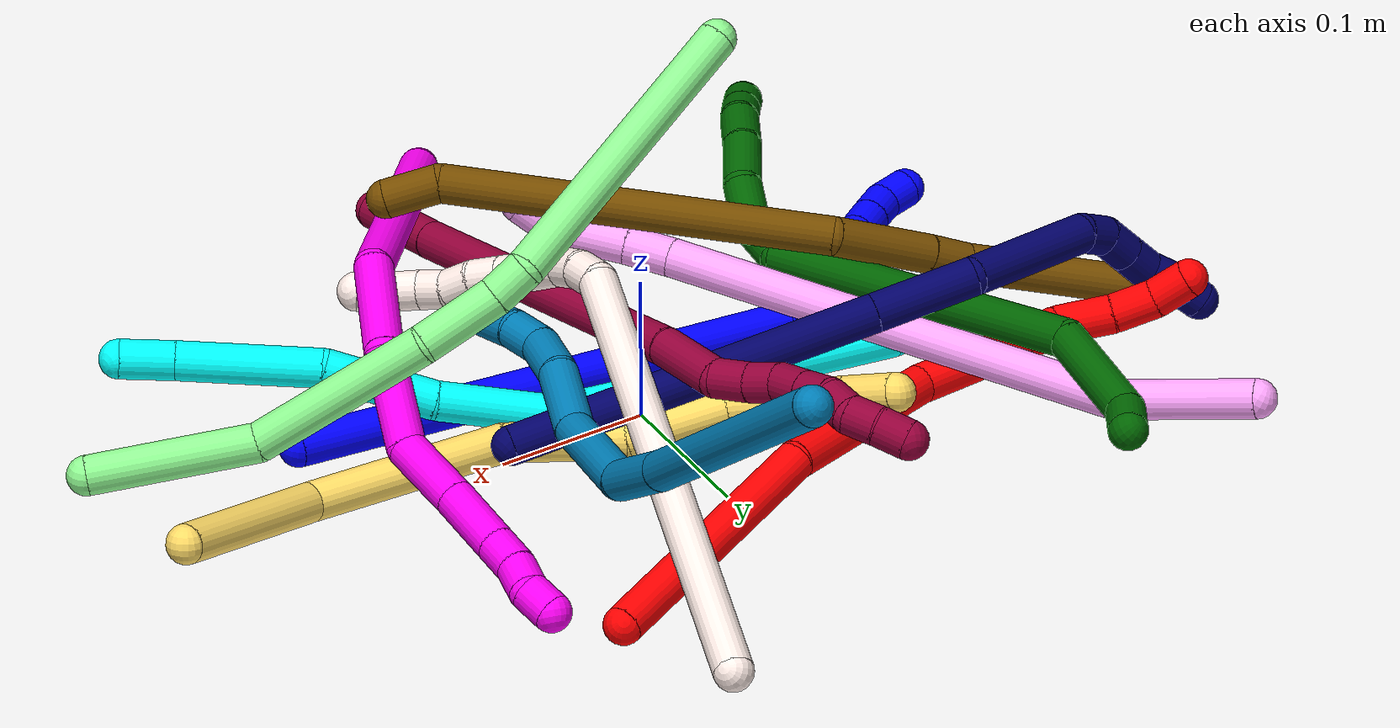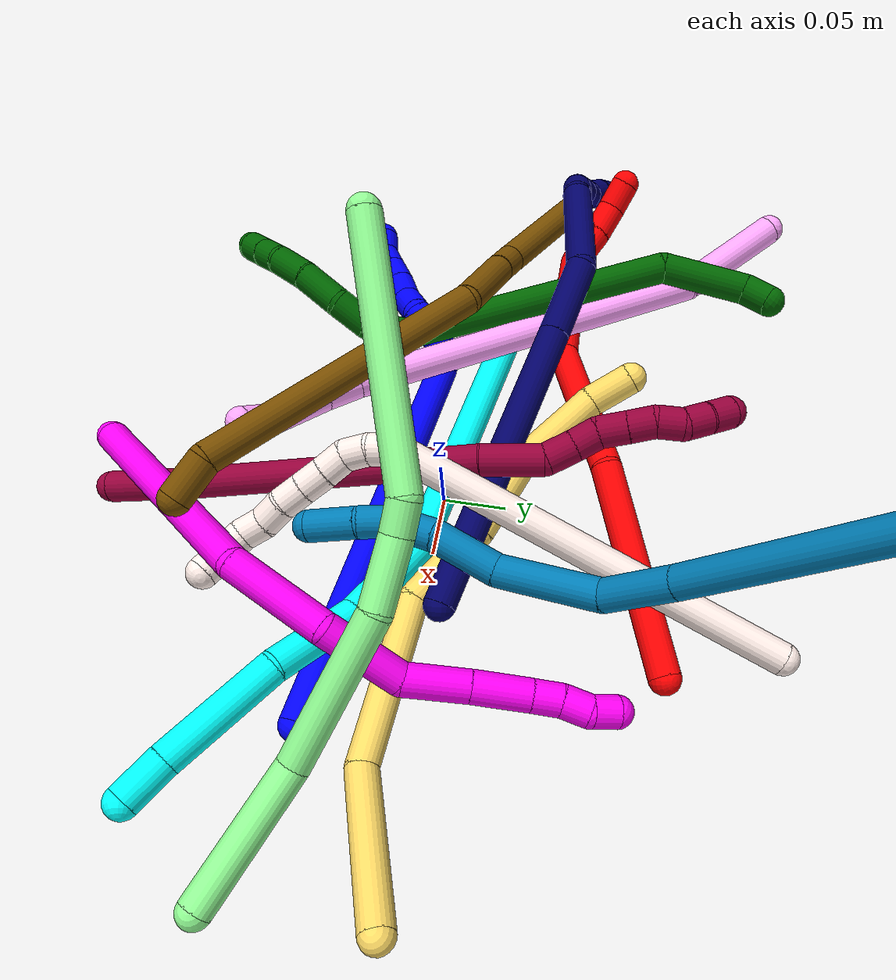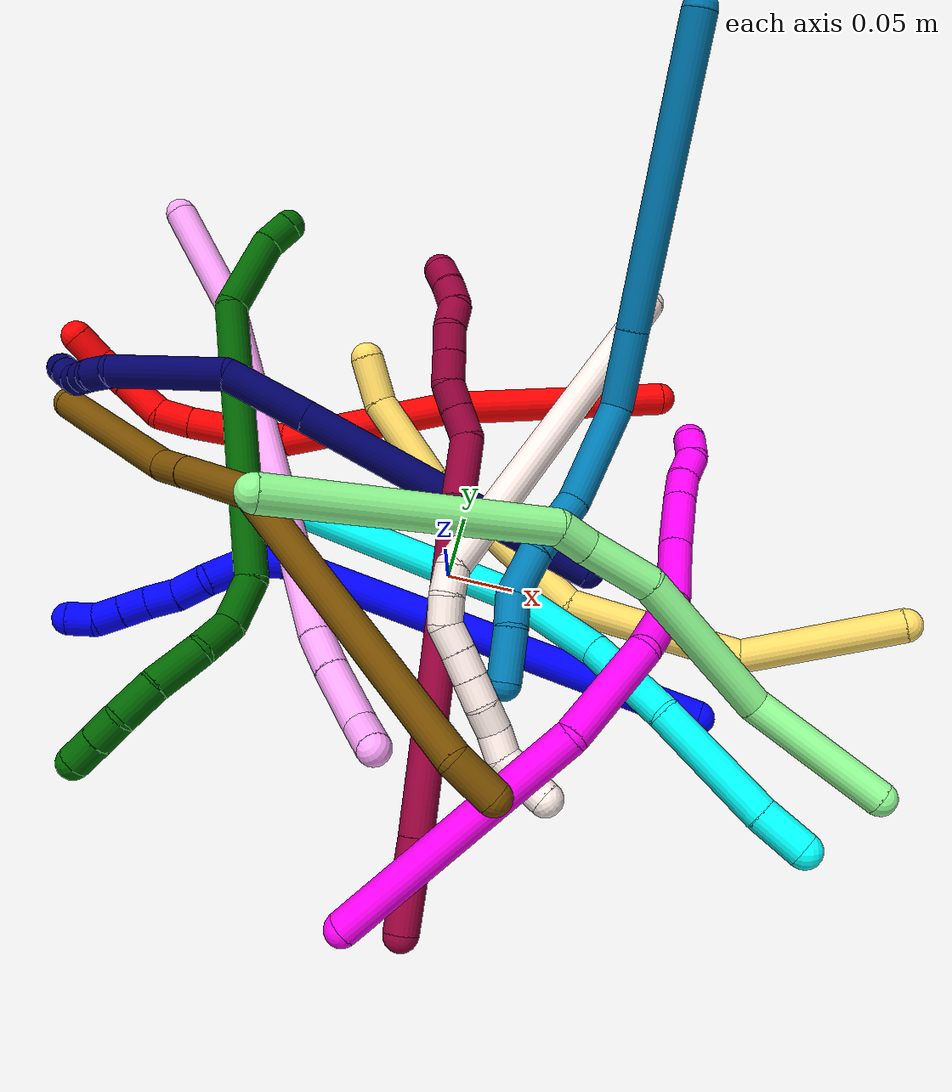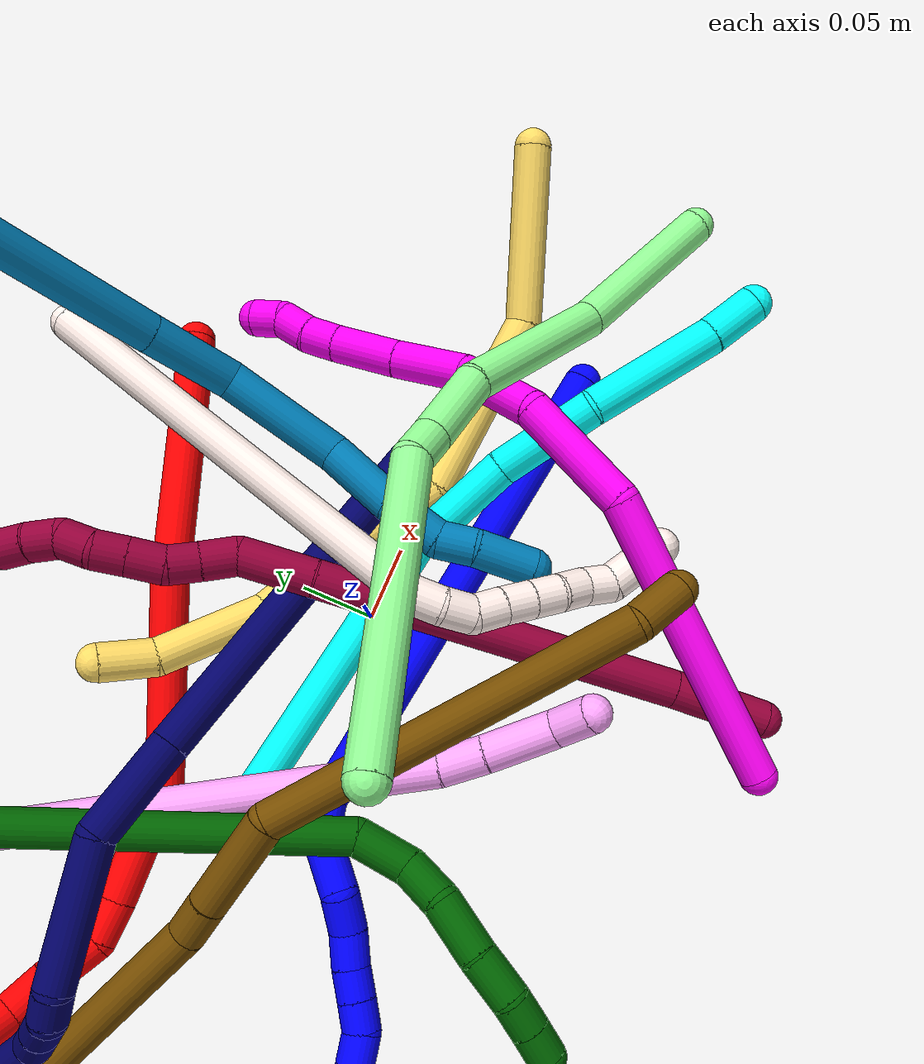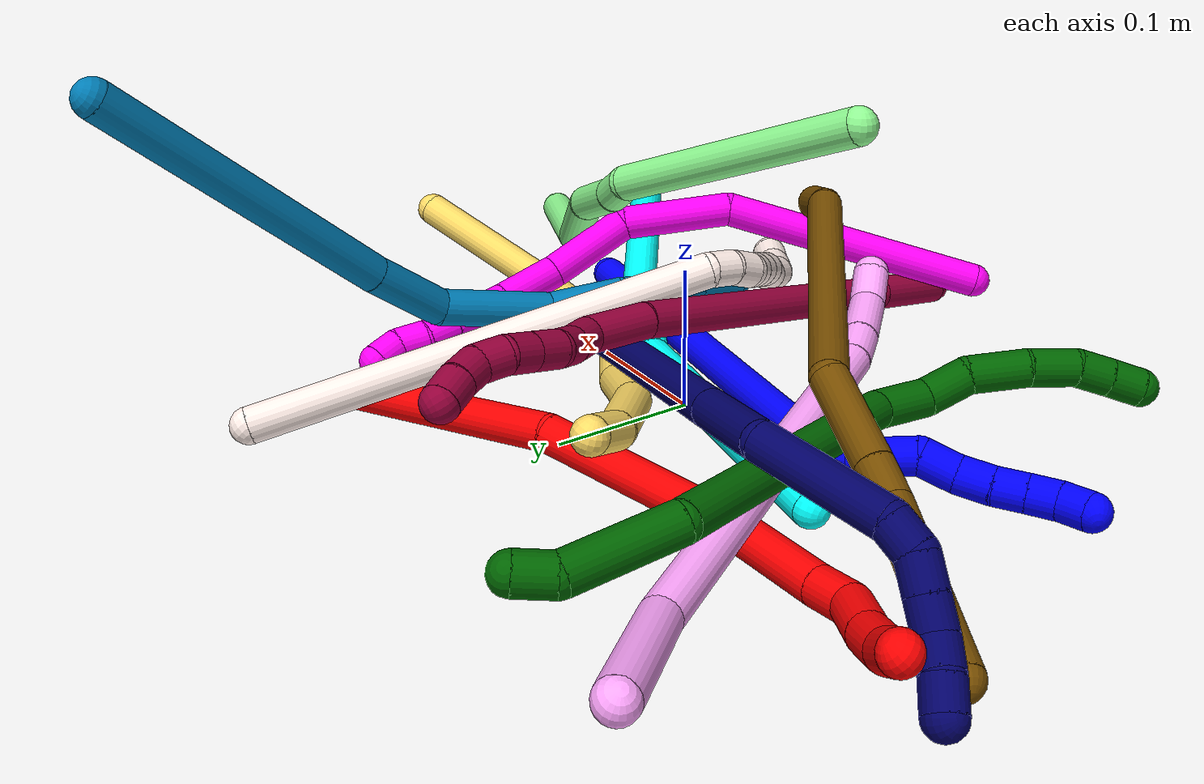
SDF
<sdf version="1.7">
 <world name="default">
  <plugin name="TubeGeneratorPlugin" filename="libtube_generator_plugin.so"/>
  <model name="photoneo_s_sensor">
   <static>1</static>
   <pose>0 0 2 1.57079 1.57079 3.14159</pose>
   <link name="link">
    <inertial><mass>0.1</mass></inertial>
    <sensor name="sensor" type="depth">
     <update_rate>30</update_rate>
     <camera>
      <horizontal_fov>1.22</horizontal_fov>
      <image><width>1920</width><height>1200</height><format>B8G8R8</format></image>
      <clip><near>0.1</near><far>4</far></clip>
      <depth_camera><output>points</output></depth_camera>
     </camera>
     <plugin name="camera_plugin" filename="libgazebo_ros_depth_camera.so">
      <baseline>0.2</baseline>
      <alwaysOn>1</alwaysOn>
      <updateRate>0.0</updateRate>
      <cameraName>camera_ir</cameraName>
      <imageTopicName>/camera/color/image_raw</imageTopicName>
      <cameraInfoTopicName>/camera/color/camera_info</cameraInfoTopicName>
      <depthImageTopicName>/camera/depth/image_raw</depthImageTopicName>
      <depthImageCameraInfoTopicName>/camera/depth/camera_info</depthImageCameraInfoTopicName>
      <pointCloudTopicName>/camera/depth/points</pointCloudTopicName>
      <frameName>fr_optical</frameName>
      <pointCloudCutoff>0.1</pointCloudCutoff>
      <pointCloudCutoffMax>2.0</pointCloudCutoffMax>
      <distortionK1>0</distortionK1>
      <distortionK2>0</distortionK2>
      <distortionK3>0</distortionK3>
      <distortionT1>0</distortionT1>
      <distortionT2>0</distortionT2>
      <CxPrime>0</CxPrime>
      <Cx>0</Cx>
      <Cy>0</Cy>
      <focalLength>0</focalLength>
      <hackBaseline>0</hackBaseline>
     </plugin>
    </sensor>
   </link>
  </model>
  <gravity>0 0 -9.8</gravity>
  <magnetic_field>6e-06 2.3e-05 -4.2e-05</magnetic_field>
  <atmosphere type="adiabatic"/>
  <physics name="default_physics" default="0" type="ode">
   <max_step_size>0.003</max_step_size>
   <real_time_factor>1</real_time_factor>
   <real_time_update_rate>1000</real_time_update_rate>
   <max_contacts>10000</max_contacts>
   <ode>
    <solver>
     <type>quick</type>
     <iters>100</iters>
     <sor>1.3</sor>
     <use_dynamic_moi_rescaling>0</use_dynamic_moi_rescaling>
    </solver>
    <constraints>
     <contact_max_correcting_vel>0</contact_max_correcting_vel>
     <contact_surface_layer>0.001</contact_surface_layer>
     <cfm>0</cfm>
     <erp>0.2</erp>
    </constraints>
   </ode>
  </physics>
  <scene><ambient>0.4 0.4 0.4 1</ambient><background>0.7 0.7 0.7 1</background><shadows>0</shadows></scene>
  <audio><device>default</device></audio>
  <spherical_coordinates>
   <surface_model>EARTH_WGS84</surface_model>
   <latitude_deg>0</latitude_deg>
   <longitude_deg>0</longitude_deg>
   <elevation>0</elevation>
   <heading_deg>0</heading_deg>
  </spherical_coordinates>
  <model name="bin">
   <static>1</static>
   <link name="bottom">
    <collision name="collision-bottom">
     <pose>0 0 -0.01 0 -0 0</pose>
     <geometry><box><size>0.8 0.6 0.02</size></box></geometry>
     <surface>
      <friction><ode><mu>100</mu><mu2>100</mu2></ode></friction>
      <contact><collide_bitmask>65535</collide_bitmask></contact>
     </surface>
    </collision>
   </link>
   <link name="west_wall">
    <collision name="collision-west_wall">
     <pose>-0.41 0 0.1 0 -0 0</pose>
     <geometry><box><size>0.02 0.6 0.2</size></box></geometry>
     <surface>
      <friction><ode><mu>100</mu><mu2>100</mu2></ode></friction>
      <contact><collide_bitmask>65535</collide_bitmask></contact>
     </surface>
    </collision>
   </link>
   <link name="east_wall">
    <collision name="collision-east_wall">
     <pose>0.41 0 0.1 0 -0 0</pose>
     <geometry><box><size>0.02 0.6 0.2</size></box></geometry>
     <surface>
      <friction><ode><mu>100</mu><mu2>100</mu2></ode></friction>
      <contact><collide_bitmask>65535</collide_bitmask></contact>
     </surface>
    </collision>
   </link>
   <link name="south_wall">
    <collision name="collision-south_wall">
     <pose>0 -0.31 0.1 0 -0 0</pose>
     <geometry><box><size>0.8 0.02 0.2</size></box></geometry>
     <surface>
      <friction><ode><mu>100</mu><mu2>100</mu2></ode></friction>
      <contact><collide_bitmask>65535</collide_bitmask></contact>
     </surface>
    </collision>
   </link>
   <link name="north_wall">
    <collision name="collision-north_wall">
     <pose>0 0.31 0.1 0 -0 0</pose>
     <geometry><box><size>0.8 0.02 0.2</size></box></geometry>
     <surface>
      <friction><ode><mu>100</mu><mu2>100</mu2></ode></friction>
      <contact><collide_bitmask>65535</collide_bitmask></contact>
     </surface>
    </collision>
   </link>
  </model>
  <model name="1">
   <static>0</static>
   <link name="1">
    <collision name="collision-cylinder-e_1_1_4">
     <pose>-0.064321 0.016195 0.150427 -0.107246 -0.401981 0.021871</pose>
     <geometry><cylinder><radius>0.0125</radius><length>0.328802</length></cylinder></geometry>
     <surface>
      <friction><ode><mu>1.16</mu><mu2>1.16</mu2><slip1>0</slip1><slip2>0</slip2></ode></friction>
      <contact><ode><kp>1e+06</kp><kd>1</kd><max_vel>0</max_vel><min_depth>0.001</min_depth></ode></contact>
     </surface>
    </collision>
    <visual name="visual-cylinder-e_1_1_4">
     <pose>-0.064321 0.016195 0.150427 -0.107246 -0.401981 0.021871</pose>
     <geometry><cylinder><radius>0.0125</radius><length>0.328802</length></cylinder></geometry>
     <material><ambient>0 0 1 1</ambient></material>
    </visual>
    <collision name="collision-cylinder-e_2_4_5">
     <pose>-0.13742 0.033699 0.308421 -0.171369 -0.852096 0.077927</pose>
     <geometry><cylinder><radius>0.0125</radius><length>0.023328</length></cylinder></geometry>
     <surface>
      <friction><ode><mu>1.16</mu><mu2>1.16</mu2><slip1>0</slip1><slip2>0</slip2></ode></friction>
      <contact><ode><kp>1e+06</kp><kd>1</kd><max_vel>0</max_vel><min_depth>0.001</min_depth></ode></contact>
     </surface>
    </collision>
    <visual name="visual-cylinder-e_2_4_5">
     <pose>-0.13742 0.033699 0.308421 -0.171369 -0.852096 0.077927</pose>
     <geometry><cylinder><radius>0.0125</radius><length>0.023328</length></cylinder></geometry>
     <material><ambient>0 0 1 1</ambient></material>
    </visual>
    <collision name="collision-cylinder-e_3_5_6">
     <pose>-0.16366 0.042329 0.320978 -0.972533 -1.1013 0.627671</pose>
     <geometry><cylinder><radius>0.0125</radius><length>0.039158</length></cylinder></geometry>
     <surface>
      <friction><ode><mu>1.16</mu><mu2>1.16</mu2><slip1>0</slip1><slip2>0</slip2></ode></friction>
      <contact><ode><kp>1e+06</kp><kd>1</kd><max_vel>0</max_vel><min_depth>0.001</min_depth></ode></contact>
     </surface>
    </collision>
    <visual name="visual-cylinder-e_3_5_6">
     <pose>-0.16366 0.042329 0.320978 -0.972533 -1.1013 0.627671</pose>
     <geometry><cylinder><radius>0.0125</radius><length>0.039158</length></cylinder></geometry>
     <material><ambient>0 0 1 1</ambient></material>
    </visual>
    <collision name="collision-cylinder-e_4_6_7">
     <pose>-0.188124 0.058375 0.331561 -1.00074 -0.594162 0.331711</pose>
     <geometry><cylinder><radius>0.0125</radius><length>0.025019</length></cylinder></geometry>
     <surface>
      <friction><ode><mu>1.16</mu><mu2>1.16</mu2><slip1>0</slip1><slip2>0</slip2></ode></friction>
      <contact><ode><kp>1e+06</kp><kd>1</kd><max_vel>0</max_vel><min_depth>0.001</min_depth></ode></contact>
     </surface>
    </collision>
    <visual name="visual-cylinder-e_4_6_7">
     <pose>-0.188124 0.058375 0.331561 -1.00074 -0.594162 0.331711</pose>
     <geometry><cylinder><radius>0.0125</radius><length>0.025019</length></cylinder></geometry>
     <material><ambient>0 0 1 1</ambient></material>
    </visual>
    <collision name="collision-cylinder-e_5_7_8">
     <pose>-0.203161 0.072715 0.343324 -0.738292 -0.766678 0.309555</pose>
     <geometry><cylinder><radius>0.0125</radius><length>0.023162</length></cylinder></geometry>
     <surface>
      <friction><ode><mu>1.16</mu><mu2>1.16</mu2><slip1>0</slip1><slip2>0</slip2></ode></friction>
      <contact><ode><kp>1e+06</kp><kd>1</kd><max_vel>0</max_vel><min_depth>0.001</min_depth></ode></contact>
     </surface>
    </collision>
    <visual name="visual-cylinder-e_5_7_8">
     <pose>-0.203161 0.072715 0.343324 -0.738292 -0.766678 0.309555</pose>
     <geometry><cylinder><radius>0.0125</radius><length>0.023162</length></cylinder></geometry>
     <material><ambient>0 0 1 1</ambient></material>
    </visual>
    <collision name="collision-cylinder-e_6_8_9">
     <pose>-0.218913 0.083216 0.353907 -0.836136 -0.864416 0.404271</pose>
     <geometry><cylinder><radius>0.0125</radius><length>0.020293</length></cylinder></geometry>
     <surface>
      <friction><ode><mu>1.16</mu><mu2>1.16</mu2><slip1>0</slip1><slip2>0</slip2></ode></friction>
      <contact><ode><kp>1e+06</kp><kd>1</kd><max_vel>0</max_vel><min_depth>0.001</min_depth></ode></contact>
     </surface>
    </collision>
    <visual name="visual-cylinder-e_6_8_9">
     <pose>-0.218913 0.083216 0.353907 -0.836136 -0.864416 0.404271</pose>
     <geometry><cylinder><radius>0.0125</radius><length>0.020293</length></cylinder></geometry>
     <material><ambient>0 0 1 1</ambient></material>
    </visual>
    <collision name="collision-cylinder-e_7_9_10">
     <pose>-0.234149 0.092933 0.362853 -0.817434 -0.848535 0.386389</pose>
     <geometry><cylinder><radius>0.0125</radius><length>0.020036</length></cylinder></geometry>
     <surface>
      <friction><ode><mu>1.16</mu><mu2>1.16</mu2><slip1>0</slip1><slip2>0</slip2></ode></friction>
      <contact><ode><kp>1e+06</kp><kd>1</kd><max_vel>0</max_vel><min_depth>0.001</min_depth></ode></contact>
     </surface>
    </collision>
    <visual name="visual-cylinder-e_7_9_10">
     <pose>-0.234149 0.092933 0.362853 -0.817434 -0.848535 0.386389</pose>
     <geometry><cylinder><radius>0.0125</radius><length>0.020036</length></cylinder></geometry>
     <material><ambient>0 0 1 1</ambient></material>
    </visual>
    <collision name="collision-cylinder-e_8_10_2">
     <pose>-0.248167 0.100206 0.374718 -0.321408 -0.699254 0.118069</pose>
     <geometry><cylinder><radius>0.0125</radius><length>0.020202</length></cylinder></geometry>
     <surface>
      <friction><ode><mu>1.16</mu><mu2>1.16</mu2><slip1>0</slip1><slip2>0</slip2></ode></friction>
      <contact><ode><kp>1e+06</kp><kd>1</kd><max_vel>0</max_vel><min_depth>0.001</min_depth></ode></contact>
     </surface>
    </collision>
    <visual name="visual-cylinder-e_8_10_2">
     <pose>-0.248167 0.100206 0.374718 -0.321408 -0.699254 0.118069</pose>
     <geometry><cylinder><radius>0.0125</radius><length>0.020202</length></cylinder></geometry>
     <material><ambient>0 0 1 1</ambient></material>
    </visual>
    <collision name="collision-sphere-2">
     <pose>-0.254668 0.102648 0.382053 0 -0 0</pose>
     <geometry><sphere><radius>0.0125</radius></sphere></geometry>
     <surface>
      <friction><ode><mu>1.16</mu><mu2>1.16</mu2><slip1>0</slip1><slip2>0</slip2></ode></friction>
      <contact><ode><kp>1e+06</kp><kd>1</kd><max_vel>0</max_vel><min_depth>0.001</min_depth></ode></contact>
     </surface>
    </collision>
    <visual name="visual-sphere-2">
     <pose>-0.254668 0.102648 0.382053 0 -0 0</pose>
     <geometry><sphere><radius>0.0125</radius></sphere></geometry>
     <material><ambient>0 0 1 1</ambient></material>
    </visual>
    <collision name="collision-sphere-10">
     <pose>-0.241665 0.097764 0.367383 0 -0 0</pose>
     <geometry><sphere><radius>0.0125</radius></sphere></geometry>
     <surface>
      <friction><ode><mu>1.16</mu><mu2>1.16</mu2><slip1>0</slip1><slip2>0</slip2></ode></friction>
      <contact><ode><kp>1e+06</kp><kd>1</kd><max_vel>0</max_vel><min_depth>0.001</min_depth></ode></contact>
     </surface>
    </collision>
    <visual name="visual-sphere-10">
     <pose>-0.241665 0.097764 0.367383 0 -0 0</pose>
     <geometry><sphere><radius>0.0125</radius></sphere></geometry>
     <material><ambient>0 0 1 1</ambient></material>
    </visual>
    <collision name="collision-sphere-9">
     <pose>-0.226632 0.088103 0.358322 0 -0 0</pose>
     <geometry><sphere><radius>0.0125</radius></sphere></geometry>
     <surface>
      <friction><ode><mu>1.16</mu><mu2>1.16</mu2><slip1>0</slip1><slip2>0</slip2></ode></friction>
      <contact><ode><kp>1e+06</kp><kd>1</kd><max_vel>0</max_vel><min_depth>0.001</min_depth></ode></contact>
     </surface>
    </collision>
    <visual name="visual-sphere-9">
     <pose>-0.226632 0.088103 0.358322 0 -0 0</pose>
     <geometry><sphere><radius>0.0125</radius></sphere></geometry>
     <material><ambient>0 0 1 1</ambient></material>
    </visual>
    <collision name="collision-sphere-4">
     <pose>-0.128641 0.03239 0.300854 0 -0 0</pose>
     <geometry><sphere><radius>0.0125</radius></sphere></geometry>
     <surface>
      <friction><ode><mu>1.16</mu><mu2>1.16</mu2><slip1>0</slip1><slip2>0</slip2></ode></friction>
      <contact><ode><kp>1e+06</kp><kd>1</kd><max_vel>0</max_vel><min_depth>0.001</min_depth></ode></contact>
     </surface>
    </collision>
    <visual name="visual-sphere-4">
     <pose>-0.128641 0.03239 0.300854 0 -0 0</pose>
     <geometry><sphere><radius>0.0125</radius></sphere></geometry>
     <material><ambient>0 0 1 1</ambient></material>
    </visual>
    <collision name="collision-sphere-1">
     <geometry><sphere><radius>0.0125</radius></sphere></geometry>
     <surface>
      <friction><ode><mu>1.16</mu><mu2>1.16</mu2><slip1>0</slip1><slip2>0</slip2></ode></friction>
      <contact><ode><kp>1e+06</kp><kd>1</kd><max_vel>0</max_vel><min_depth>0.001</min_depth></ode></contact>
     </surface>
    </collision>
    <visual name="visual-sphere-1">
     <geometry><sphere><radius>0.0125</radius></sphere></geometry>
     <material><ambient>0 0 1 1</ambient></material>
    </visual>
    <collision name="collision-sphere-8">
     <pose>-0.211195 0.078328 0.349493 0 -0 0</pose>
     <geometry><sphere><radius>0.0125</radius></sphere></geometry>
     <surface>
      <friction><ode><mu>1.16</mu><mu2>1.16</mu2><slip1>0</slip1><slip2>0</slip2></ode></friction>
      <contact><ode><kp>1e+06</kp><kd>1</kd><max_vel>0</max_vel><min_depth>0.001</min_depth></ode></contact>
     </surface>
    </collision>
    <visual name="visual-sphere-8">
     <pose>-0.211195 0.078328 0.349493 0 -0 0</pose>
     <geometry><sphere><radius>0.0125</radius></sphere></geometry>
     <material><ambient>0 0 1 1</ambient></material>
    </visual>
    <collision name="collision-sphere-5">
     <pose>-0.1462 0.035009 0.315989 0 -0 0</pose>
     <geometry><sphere><radius>0.0125</radius></sphere></geometry>
     <surface>
      <friction><ode><mu>1.16</mu><mu2>1.16</mu2><slip1>0</slip1><slip2>0</slip2></ode></friction>
      <contact><ode><kp>1e+06</kp><kd>1</kd><max_vel>0</max_vel><min_depth>0.001</min_depth></ode></contact>
     </surface>
    </collision>
    <visual name="visual-sphere-5">
     <pose>-0.1462 0.035009 0.315989 0 -0 0</pose>
     <geometry><sphere><radius>0.0125</radius></sphere></geometry>
     <material><ambient>0 0 1 1</ambient></material>
    </visual>
    <collision name="collision-sphere-6">
     <pose>-0.181121 0.049649 0.325967 0 -0 0</pose>
     <geometry><sphere><radius>0.0125</radius></sphere></geometry>
     <surface>
      <friction><ode><mu>1.16</mu><mu2>1.16</mu2><slip1>0</slip1><slip2>0</slip2></ode></friction>
      <contact><ode><kp>1e+06</kp><kd>1</kd><max_vel>0</max_vel><min_depth>0.001</min_depth></ode></contact>
     </surface>
    </collision>
    <visual name="visual-sphere-6">
     <pose>-0.181121 0.049649 0.325967 0 -0 0</pose>
     <geometry><sphere><radius>0.0125</radius></sphere></geometry>
     <material><ambient>0 0 1 1</ambient></material>
    </visual>
    <collision name="collision-sphere-7">
     <pose>-0.195127 0.067101 0.337155 0 -0 0</pose>
     <geometry><sphere><radius>0.0125</radius></sphere></geometry>
     <surface>
      <friction><ode><mu>1.16</mu><mu2>1.16</mu2><slip1>0</slip1><slip2>0</slip2></ode></friction>
      <contact><ode><kp>1e+06</kp><kd>1</kd><max_vel>0</max_vel><min_depth>0.001</min_depth></ode></contact>
     </surface>
    </collision>
    <visual name="visual-sphere-7">
     <pose>-0.195127 0.067101 0.337155 0 -0 0</pose>
     <geometry><sphere><radius>0.0125</radius></sphere></geometry>
     <material><ambient>0 0 1 1</ambient></material>
    </visual>
    <inertial>
     <pose>-0.108645 0.032977 0.214988 0 -0 0</pose>
     <mass>0.5</mass>
     <inertia>
      <ixx>0.002791</ixx>
      <ixy>0</ixy>
      <ixz>0</ixz>
      <iyy>0.003046</iyy>
      <iyz>0</iyz>
      <izz>0.000907</izz>
     </inertia>
    </inertial>
   </link>
   <pose>0.204604 -0.068253 0.011626 -1.75597 0.595034 0.94489</pose>
  </model>
  <model name="2">
   <static>0</static>
   <link name="2">
    <collision name="collision-cylinder-e_1_1_4">
     <pose>-0.074376 -0.023233 0.037831 0.550752 -1.03266 -0.3181</pose>
     <geometry><cylinder><radius>0.0125</radius><length>0.173237</length></cylinder></geometry>
     <surface>
      <friction><ode><mu>1.16</mu><mu2>1.16</mu2><slip1>0</slip1><slip2>0</slip2></ode></friction>
      <contact><ode><kp>1e+06</kp><kd>1</kd><max_vel>0</max_vel><min_depth>0.001</min_depth></ode></contact>
     </surface>
    </collision>
    <visual name="visual-cylinder-e_1_1_4">
     <pose>-0.074376 -0.023233 0.037831 0.550752 -1.03266 -0.3181</pose>
     <geometry><cylinder><radius>0.0125</radius><length>0.173237</length></cylinder></geometry>
     <material><ambient>1 0 0 1</ambient></material>
    </visual>
    <collision name="collision-cylinder-e_2_4_5">
     <pose>-0.19493 -0.069281 0.117734 0.496887 -0.767515 -0.204152</pose>
     <geometry><cylinder><radius>0.0125</radius><length>0.133011</length></cylinder></geometry>
     <surface>
      <friction><ode><mu>1.16</mu><mu2>1.16</mu2><slip1>0</slip1><slip2>0</slip2></ode></friction>
      <contact><ode><kp>1e+06</kp><kd>1</kd><max_vel>0</max_vel><min_depth>0.001</min_depth></ode></contact>
     </surface>
    </collision>
    <visual name="visual-cylinder-e_2_4_5">
     <pose>-0.19493 -0.069281 0.117734 0.496887 -0.767515 -0.204152</pose>
     <geometry><cylinder><radius>0.0125</radius><length>0.133011</length></cylinder></geometry>
     <material><ambient>1 0 0 1</ambient></material>
    </visual>
    <collision name="collision-cylinder-e_3_5_6">
     <pose>-0.269728 -0.114662 0.173634 1.02104 -0.824484 -0.480354</pose>
     <geometry><cylinder><radius>0.0125</radius><length>0.077964</length></cylinder></geometry>
     <surface>
      <friction><ode><mu>1.16</mu><mu2>1.16</mu2><slip1>0</slip1><slip2>0</slip2></ode></friction>
      <contact><ode><kp>1e+06</kp><kd>1</kd><max_vel>0</max_vel><min_depth>0.001</min_depth></ode></contact>
     </surface>
    </collision>
    <visual name="visual-cylinder-e_3_5_6">
     <pose>-0.269728 -0.114662 0.173634 1.02104 -0.824484 -0.480354</pose>
     <geometry><cylinder><radius>0.0125</radius><length>0.077964</length></cylinder></geometry>
     <material><ambient>1 0 0 1</ambient></material>
    </visual>
    <collision name="collision-cylinder-e_4_6_7">
     <pose>-0.309079 -0.144899 0.190662 1.17559 -0.911775 -0.631616</pose>
     <geometry><cylinder><radius>0.0125</radius><length>0.027145</length></cylinder></geometry>
     <surface>
      <friction><ode><mu>1.16</mu><mu2>1.16</mu2><slip1>0</slip1><slip2>0</slip2></ode></friction>
      <contact><ode><kp>1e+06</kp><kd>1</kd><max_vel>0</max_vel><min_depth>0.001</min_depth></ode></contact>
     </surface>
    </collision>
    <visual name="visual-cylinder-e_4_6_7">
     <pose>-0.309079 -0.144899 0.190662 1.17559 -0.911775 -0.631616</pose>
     <geometry><cylinder><radius>0.0125</radius><length>0.027145</length></cylinder></geometry>
     <material><ambient>1 0 0 1</ambient></material>
    </visual>
    <collision name="collision-cylinder-e_5_7_8">
     <pose>-0.33043 -0.166855 0.191658 1.72383 -0.633669 -0.730361</pose>
     <geometry><cylinder><radius>0.0125</radius><length>0.035874</length></cylinder></geometry>
     <surface>
      <friction><ode><mu>1.16</mu><mu2>1.16</mu2><slip1>0</slip1><slip2>0</slip2></ode></friction>
      <contact><ode><kp>1e+06</kp><kd>1</kd><max_vel>0</max_vel><min_depth>0.001</min_depth></ode></contact>
     </surface>
    </collision>
    <visual name="visual-cylinder-e_5_7_8">
     <pose>-0.33043 -0.166855 0.191658 1.72383 -0.633669 -0.730361</pose>
     <geometry><cylinder><radius>0.0125</radius><length>0.035874</length></cylinder></geometry>
     <material><ambient>1 0 0 1</ambient></material>
    </visual>
    <collision name="collision-cylinder-e_6_8_9">
     <pose>-0.350727 -0.190916 0.187266 1.79111 -0.768077 -0.934656</pose>
     <geometry><cylinder><radius>0.0125</radius><length>0.027856</length></cylinder></geometry>
     <surface>
      <friction><ode><mu>1.16</mu><mu2>1.16</mu2><slip1>0</slip1><slip2>0</slip2></ode></friction>
      <contact><ode><kp>1e+06</kp><kd>1</kd><max_vel>0</max_vel><min_depth>0.001</min_depth></ode></contact>
     </surface>
    </collision>
    <visual name="visual-cylinder-e_6_8_9">
     <pose>-0.350727 -0.190916 0.187266 1.79111 -0.768077 -0.934656</pose>
     <geometry><cylinder><radius>0.0125</radius><length>0.027856</length></cylinder></geometry>
     <material><ambient>1 0 0 1</ambient></material>
    </visual>
    <collision name="collision-cylinder-e_7_9_2">
     <pose>-0.369663 -0.207413 0.180151 2.20323 -0.838023 -1.44171</pose>
     <geometry><cylinder><radius>0.0125</radius><length>0.024913</length></cylinder></geometry>
     <surface>
      <friction><ode><mu>1.16</mu><mu2>1.16</mu2><slip1>0</slip1><slip2>0</slip2></ode></friction>
      <contact><ode><kp>1e+06</kp><kd>1</kd><max_vel>0</max_vel><min_depth>0.001</min_depth></ode></contact>
     </surface>
    </collision>
    <visual name="visual-cylinder-e_7_9_2">
     <pose>-0.369663 -0.207413 0.180151 2.20323 -0.838023 -1.44171</pose>
     <geometry><cylinder><radius>0.0125</radius><length>0.024913</length></cylinder></geometry>
     <material><ambient>1 0 0 1</ambient></material>
    </visual>
    <collision name="collision-sphere-2">
     <pose>-0.378922 -0.214134 0.175225 0 -0 0</pose>
     <geometry><sphere><radius>0.0125</radius></sphere></geometry>
     <surface>
      <friction><ode><mu>1.16</mu><mu2>1.16</mu2><slip1>0</slip1><slip2>0</slip2></ode></friction>
      <contact><ode><kp>1e+06</kp><kd>1</kd><max_vel>0</max_vel><min_depth>0.001</min_depth></ode></contact>
     </surface>
    </collision>
    <visual name="visual-sphere-2">
     <pose>-0.378922 -0.214134 0.175225 0 -0 0</pose>
     <geometry><sphere><radius>0.0125</radius></sphere></geometry>
     <material><ambient>1 0 0 1</ambient></material>
    </visual>
    <collision name="collision-sphere-9">
     <pose>-0.360404 -0.200692 0.185076 0 -0 0</pose>
     <geometry><sphere><radius>0.0125</radius></sphere></geometry>
     <surface>
      <friction><ode><mu>1.16</mu><mu2>1.16</mu2><slip1>0</slip1><slip2>0</slip2></ode></friction>
      <contact><ode><kp>1e+06</kp><kd>1</kd><max_vel>0</max_vel><min_depth>0.001</min_depth></ode></contact>
     </surface>
    </collision>
    <visual name="visual-sphere-9">
     <pose>-0.360404 -0.200692 0.185076 0 -0 0</pose>
     <geometry><sphere><radius>0.0125</radius></sphere></geometry>
     <material><ambient>1 0 0 1</ambient></material>
    </visual>
    <collision name="collision-sphere-4">
     <pose>-0.148752 -0.046467 0.075662 0 -0 0</pose>
     <geometry><sphere><radius>0.0125</radius></sphere></geometry>
     <surface>
      <friction><ode><mu>1.16</mu><mu2>1.16</mu2><slip1>0</slip1><slip2>0</slip2></ode></friction>
      <contact><ode><kp>1e+06</kp><kd>1</kd><max_vel>0</max_vel><min_depth>0.001</min_depth></ode></contact>
     </surface>
    </collision>
    <visual name="visual-sphere-4">
     <pose>-0.148752 -0.046467 0.075662 0 -0 0</pose>
     <geometry><sphere><radius>0.0125</radius></sphere></geometry>
     <material><ambient>1 0 0 1</ambient></material>
    </visual>
    <collision name="collision-sphere-1">
     <geometry><sphere><radius>0.0125</radius></sphere></geometry>
     <surface>
      <friction><ode><mu>1.16</mu><mu2>1.16</mu2><slip1>0</slip1><slip2>0</slip2></ode></friction>
      <contact><ode><kp>1e+06</kp><kd>1</kd><max_vel>0</max_vel><min_depth>0.001</min_depth></ode></contact>
     </surface>
    </collision>
    <visual name="visual-sphere-1">
     <geometry><sphere><radius>0.0125</radius></sphere></geometry>
     <material><ambient>1 0 0 1</ambient></material>
    </visual>
    <collision name="collision-sphere-8">
     <pose>-0.34105 -0.181141 0.189455 0 -0 0</pose>
     <geometry><sphere><radius>0.0125</radius></sphere></geometry>
     <surface>
      <friction><ode><mu>1.16</mu><mu2>1.16</mu2><slip1>0</slip1><slip2>0</slip2></ode></friction>
      <contact><ode><kp>1e+06</kp><kd>1</kd><max_vel>0</max_vel><min_depth>0.001</min_depth></ode></contact>
     </surface>
    </collision>
    <visual name="visual-sphere-8">
     <pose>-0.34105 -0.181141 0.189455 0 -0 0</pose>
     <geometry><sphere><radius>0.0125</radius></sphere></geometry>
     <material><ambient>1 0 0 1</ambient></material>
    </visual>
    <collision name="collision-sphere-5">
     <pose>-0.241108 -0.092095 0.159806 0 -0 0</pose>
     <geometry><sphere><radius>0.0125</radius></sphere></geometry>
     <surface>
      <friction><ode><mu>1.16</mu><mu2>1.16</mu2><slip1>0</slip1><slip2>0</slip2></ode></friction>
      <contact><ode><kp>1e+06</kp><kd>1</kd><max_vel>0</max_vel><min_depth>0.001</min_depth></ode></contact>
     </surface>
    </collision>
    <visual name="visual-sphere-5">
     <pose>-0.241108 -0.092095 0.159806 0 -0 0</pose>
     <geometry><sphere><radius>0.0125</radius></sphere></geometry>
     <material><ambient>1 0 0 1</ambient></material>
    </visual>
    <collision name="collision-sphere-6">
     <pose>-0.298349 -0.137228 0.187462 0 -0 0</pose>
     <geometry><sphere><radius>0.0125</radius></sphere></geometry>
     <surface>
      <friction><ode><mu>1.16</mu><mu2>1.16</mu2><slip1>0</slip1><slip2>0</slip2></ode></friction>
      <contact><ode><kp>1e+06</kp><kd>1</kd><max_vel>0</max_vel><min_depth>0.001</min_depth></ode></contact>
     </surface>
    </collision>
    <visual name="visual-sphere-6">
     <pose>-0.298349 -0.137228 0.187462 0 -0 0</pose>
     <geometry><sphere><radius>0.0125</radius></sphere></geometry>
     <material><ambient>1 0 0 1</ambient></material>
    </visual>
    <collision name="collision-sphere-7">
     <pose>-0.319809 -0.152569 0.193862 0 -0 0</pose>
     <geometry><sphere><radius>0.0125</radius></sphere></geometry>
     <surface>
      <friction><ode><mu>1.16</mu><mu2>1.16</mu2><slip1>0</slip1><slip2>0</slip2></ode></friction>
      <contact><ode><kp>1e+06</kp><kd>1</kd><max_vel>0</max_vel><min_depth>0.001</min_depth></ode></contact>
     </surface>
    </collision>
    <visual name="visual-sphere-7">
     <pose>-0.319809 -0.152569 0.193862 0 -0 0</pose>
     <geometry><sphere><radius>0.0125</radius></sphere></geometry>
     <material><ambient>1 0 0 1</ambient></material>
    </visual>
    <inertial>
     <pose>-0.19813 -0.085168 0.115013 0 -0 0</pose>
     <mass>0.5</mass>
     <inertia>
      <ixx>0.000238</ixx>
      <ixy>0</ixy>
      <ixz>0</ixz>
      <iyy>0.000506</iyy>
      <iyz>0</iyz>
      <izz>0.000792</izz>
     </inertia>
    </inertial>
   </link>
   <pose>0.127655 0.188297 0.011474 2.7295 0.652305 0.442909</pose>
  </model>
  <model name="3">
   <static>0</static>
   <link name="3">
    <collision name="collision-cylinder-e_1_1_4">
     <pose>0.045369 -0.010162 0.103135 0.09821 0.412641 0.020571</pose>
     <geometry><cylinder><radius>0.0125</radius><length>0.226261</length></cylinder></geometry>
     <surface>
      <friction><ode><mu>1.16</mu><mu2>1.16</mu2><slip1>0</slip1><slip2>0</slip2></ode></friction>
      <contact><ode><kp>1e+06</kp><kd>1</kd><max_vel>0</max_vel><min_depth>0.001</min_depth></ode></contact>
     </surface>
    </collision>
    <visual name="visual-cylinder-e_1_1_4">
     <pose>0.045369 -0.010162 0.103135 0.09821 0.412641 0.020571</pose>
     <geometry><cylinder><radius>0.0125</radius><length>0.226261</length></cylinder></geometry>
     <material><ambient>0.003922 1 0.996078 1</ambient></material>
    </visual>
    <collision name="collision-cylinder-e_2_4_5">
     <pose>0.110713 -0.03498 0.235279 0.467855 0.551114 0.13455</pose>
     <geometry><cylinder><radius>0.0125</radius><length>0.076297</length></cylinder></geometry>
     <surface>
      <friction><ode><mu>1.16</mu><mu2>1.16</mu2><slip1>0</slip1><slip2>0</slip2></ode></friction>
      <contact><ode><kp>1e+06</kp><kd>1</kd><max_vel>0</max_vel><min_depth>0.001</min_depth></ode></contact>
     </surface>
    </collision>
    <visual name="visual-cylinder-e_2_4_5">
     <pose>0.110713 -0.03498 0.235279 0.467855 0.551114 0.13455</pose>
     <geometry><cylinder><radius>0.0125</radius><length>0.076297</length></cylinder></geometry>
     <material><ambient>0.003922 1 0.996078 1</ambient></material>
    </visual>
    <collision name="collision-cylinder-e_3_5_6">
     <pose>0.151492 -0.067876 0.286921 0.678273 0.621159 0.225492</pose>
     <geometry><cylinder><radius>0.0125</radius><length>0.071491</length></cylinder></geometry>
     <surface>
      <friction><ode><mu>1.16</mu><mu2>1.16</mu2><slip1>0</slip1><slip2>0</slip2></ode></friction>
      <contact><ode><kp>1e+06</kp><kd>1</kd><max_vel>0</max_vel><min_depth>0.001</min_depth></ode></contact>
     </surface>
    </collision>
    <visual name="visual-cylinder-e_3_5_6">
     <pose>0.151492 -0.067876 0.286921 0.678273 0.621159 0.225492</pose>
     <geometry><cylinder><radius>0.0125</radius><length>0.071491</length></cylinder></geometry>
     <material><ambient>0.003922 1 0.996078 1</ambient></material>
    </visual>
    <collision name="collision-cylinder-e_4_6_7">
     <pose>0.204734 -0.098512 0.33908 0.397541 0.791845 0.167997</pose>
     <geometry><cylinder><radius>0.0125</radius><length>0.091164</length></cylinder></geometry>
     <surface>
      <friction><ode><mu>1.16</mu><mu2>1.16</mu2><slip1>0</slip1><slip2>0</slip2></ode></friction>
      <contact><ode><kp>1e+06</kp><kd>1</kd><max_vel>0</max_vel><min_depth>0.001</min_depth></ode></contact>
     </surface>
    </collision>
    <visual name="visual-cylinder-e_4_6_7">
     <pose>0.204734 -0.098512 0.33908 0.397541 0.791845 0.167997</pose>
     <geometry><cylinder><radius>0.0125</radius><length>0.091164</length></cylinder></geometry>
     <material><ambient>0.003922 1 0.996078 1</ambient></material>
    </visual>
    <collision name="collision-cylinder-e_5_7_2">
     <pose>0.248239 -0.115695 0.381142 0.364656 0.689661 0.132255</pose>
     <geometry><cylinder><radius>0.0125</radius><length>0.034788</length></cylinder></geometry>
     <surface>
      <friction><ode><mu>1.16</mu><mu2>1.16</mu2><slip1>0</slip1><slip2>0</slip2></ode></friction>
      <contact><ode><kp>1e+06</kp><kd>1</kd><max_vel>0</max_vel><min_depth>0.001</min_depth></ode></contact>
     </surface>
    </collision>
    <visual name="visual-cylinder-e_5_7_2">
     <pose>0.248239 -0.115695 0.381142 0.364656 0.689661 0.132255</pose>
     <geometry><cylinder><radius>0.0125</radius><length>0.034788</length></cylinder></geometry>
     <material><ambient>0.003922 1 0.996078 1</ambient></material>
    </visual>
    <collision name="collision-sphere-2">
     <pose>0.259307 -0.120481 0.393679 0 -0 0</pose>
     <geometry><sphere><radius>0.0125</radius></sphere></geometry>
     <surface>
      <friction><ode><mu>1.16</mu><mu2>1.16</mu2><slip1>0</slip1><slip2>0</slip2></ode></friction>
      <contact><ode><kp>1e+06</kp><kd>1</kd><max_vel>0</max_vel><min_depth>0.001</min_depth></ode></contact>
     </surface>
    </collision>
    <visual name="visual-sphere-2">
     <pose>0.259307 -0.120481 0.393679 0 -0 0</pose>
     <geometry><sphere><radius>0.0125</radius></sphere></geometry>
     <material><ambient>0.003922 1 0.996078 1</ambient></material>
    </visual>
    <collision name="collision-sphere-7">
     <pose>0.237172 -0.11091 0.368606 0 -0 0</pose>
     <geometry><sphere><radius>0.0125</radius></sphere></geometry>
     <surface>
      <friction><ode><mu>1.16</mu><mu2>1.16</mu2><slip1>0</slip1><slip2>0</slip2></ode></friction>
      <contact><ode><kp>1e+06</kp><kd>1</kd><max_vel>0</max_vel><min_depth>0.001</min_depth></ode></contact>
     </surface>
    </collision>
    <visual name="visual-sphere-7">
     <pose>0.237172 -0.11091 0.368606 0 -0 0</pose>
     <geometry><sphere><radius>0.0125</radius></sphere></geometry>
     <material><ambient>0.003922 1 0.996078 1</ambient></material>
    </visual>
    <collision name="collision-sphere-6">
     <pose>0.172295 -0.086115 0.309555 0 -0 0</pose>
     <geometry><sphere><radius>0.0125</radius></sphere></geometry>
     <surface>
      <friction><ode><mu>1.16</mu><mu2>1.16</mu2><slip1>0</slip1><slip2>0</slip2></ode></friction>
      <contact><ode><kp>1e+06</kp><kd>1</kd><max_vel>0</max_vel><min_depth>0.001</min_depth></ode></contact>
     </surface>
    </collision>
    <visual name="visual-sphere-6">
     <pose>0.172295 -0.086115 0.309555 0 -0 0</pose>
     <geometry><sphere><radius>0.0125</radius></sphere></geometry>
     <material><ambient>0.003922 1 0.996078 1</ambient></material>
    </visual>
    <collision name="collision-sphere-5">
     <pose>0.130689 -0.049637 0.264287 0 -0 0</pose>
     <geometry><sphere><radius>0.0125</radius></sphere></geometry>
     <surface>
      <friction><ode><mu>1.16</mu><mu2>1.16</mu2><slip1>0</slip1><slip2>0</slip2></ode></friction>
      <contact><ode><kp>1e+06</kp><kd>1</kd><max_vel>0</max_vel><min_depth>0.001</min_depth></ode></contact>
     </surface>
    </collision>
    <visual name="visual-sphere-5">
     <pose>0.130689 -0.049637 0.264287 0 -0 0</pose>
     <geometry><sphere><radius>0.0125</radius></sphere></geometry>
     <material><ambient>0.003922 1 0.996078 1</ambient></material>
    </visual>
    <collision name="collision-sphere-1">
     <geometry><sphere><radius>0.0125</radius></sphere></geometry>
     <surface>
      <friction><ode><mu>1.16</mu><mu2>1.16</mu2><slip1>0</slip1><slip2>0</slip2></ode></friction>
      <contact><ode><kp>1e+06</kp><kd>1</kd><max_vel>0</max_vel><min_depth>0.001</min_depth></ode></contact>
     </surface>
    </collision>
    <visual name="visual-sphere-1">
     <geometry><sphere><radius>0.0125</radius></sphere></geometry>
     <material><ambient>0.003922 1 0.996078 1</ambient></material>
    </visual>
    <collision name="collision-sphere-4">
     <pose>0.090737 -0.020323 0.206271 0 -0 0</pose>
     <geometry><sphere><radius>0.0125</radius></sphere></geometry>
     <surface>
      <friction><ode><mu>1.16</mu><mu2>1.16</mu2><slip1>0</slip1><slip2>0</slip2></ode></friction>
      <contact><ode><kp>1e+06</kp><kd>1</kd><max_vel>0</max_vel><min_depth>0.001</min_depth></ode></contact>
     </surface>
    </collision>
    <visual name="visual-sphere-4">
     <pose>0.090737 -0.020323 0.206271 0 -0 0</pose>
     <geometry><sphere><radius>0.0125</radius></sphere></geometry>
     <material><ambient>0.003922 1 0.996078 1</ambient></material>
    </visual>
    <inertial>
     <pose>0.113685 -0.045652 0.211939 0 -0 0</pose>
     <mass>0.5</mass>
     <inertia>
      <ixx>0.00106</ixx>
      <ixy>0</ixy>
      <ixz>0</ixz>
      <iyy>0.001131</iyy>
      <iyz>0</iyz>
      <izz>-0.000311</izz>
     </inertia>
    </inertial>
   </link>
   <pose>-0.168275 0.026631 0.012626 -1.45761 0.424065 -1.27228</pose>
  </model>
  <model name="4">
   <static>0</static>
   <link name="4">
    <collision name="collision-cylinder-e_1_1_4">
     <pose>0.007569 -0.036116 -0.025963 2.19409 0.168548 0.326597</pose>
     <geometry><cylinder><radius>0.0125</radius><length>0.090238</length></cylinder></geometry>
     <surface>
      <friction><ode><mu>1.16</mu><mu2>1.16</mu2><slip1>0</slip1><slip2>0</slip2></ode></friction>
      <contact><ode><kp>1e+06</kp><kd>1</kd><max_vel>0</max_vel><min_depth>0.001</min_depth></ode></contact>
     </surface>
    </collision>
    <visual name="visual-cylinder-e_1_1_4">
     <pose>0.007569 -0.036116 -0.025963 2.19409 0.168548 0.326597</pose>
     <geometry><cylinder><radius>0.0125</radius><length>0.090238</length></cylinder></geometry>
     <material><ambient>1 0.65098 0.996078 1</ambient></material>
    </visual>
    <collision name="collision-cylinder-e_2_4_5">
     <pose>0.025771 -0.216247 -0.101269 1.90088 0.069739 0.097575</pose>
     <geometry><cylinder><radius>0.0125</radius><length>0.30521</length></cylinder></geometry>
     <surface>
      <friction><ode><mu>1.16</mu><mu2>1.16</mu2><slip1>0</slip1><slip2>0</slip2></ode></friction>
      <contact><ode><kp>1e+06</kp><kd>1</kd><max_vel>0</max_vel><min_depth>0.001</min_depth></ode></contact>
     </surface>
    </collision>
    <visual name="visual-cylinder-e_2_4_5">
     <pose>0.025771 -0.216247 -0.101269 1.90088 0.069739 0.097575</pose>
     <geometry><cylinder><radius>0.0125</radius><length>0.30521</length></cylinder></geometry>
     <material><ambient>1 0.65098 0.996078 1</ambient></material>
    </visual>
    <collision name="collision-cylinder-e_3_5_6">
     <pose>0.039943 -0.373985 -0.155159 1.89085 0.240016 0.330962</pose>
     <geometry><cylinder><radius>0.0125</radius><length>0.029765</length></cylinder></geometry>
     <surface>
      <friction><ode><mu>1.16</mu><mu2>1.16</mu2><slip1>0</slip1><slip2>0</slip2></ode></friction>
      <contact><ode><kp>1e+06</kp><kd>1</kd><max_vel>0</max_vel><min_depth>0.001</min_depth></ode></contact>
     </surface>
    </collision>
    <visual name="visual-cylinder-e_3_5_6">
     <pose>0.039943 -0.373985 -0.155159 1.89085 0.240016 0.330962</pose>
     <geometry><cylinder><radius>0.0125</radius><length>0.029765</length></cylinder></geometry>
     <material><ambient>1 0.65098 0.996078 1</ambient></material>
    </visual>
    <collision name="collision-cylinder-e_4_6_7">
     <pose>0.050038 -0.408904 -0.167649 1.92928 0.281955 0.403874</pose>
     <geometry><cylinder><radius>0.0125</radius><length>0.047133</length></cylinder></geometry>
     <surface>
      <friction><ode><mu>1.16</mu><mu2>1.16</mu2><slip1>0</slip1><slip2>0</slip2></ode></friction>
      <contact><ode><kp>1e+06</kp><kd>1</kd><max_vel>0</max_vel><min_depth>0.001</min_depth></ode></contact>
     </surface>
    </collision>
    <visual name="visual-cylinder-e_4_6_7">
     <pose>0.050038 -0.408904 -0.167649 1.92928 0.281955 0.403874</pose>
     <geometry><cylinder><radius>0.0125</radius><length>0.047133</length></cylinder></geometry>
     <material><ambient>1 0.65098 0.996078 1</ambient></material>
    </visual>
    <collision name="collision-cylinder-e_5_7_2">
     <pose>0.062589 -0.442443 -0.173877 1.43277 0.448328 0.391934</pose>
     <geometry><cylinder><radius>0.0125</radius><length>0.027654</length></cylinder></geometry>
     <surface>
      <friction><ode><mu>1.16</mu><mu2>1.16</mu2><slip1>0</slip1><slip2>0</slip2></ode></friction>
      <contact><ode><kp>1e+06</kp><kd>1</kd><max_vel>0</max_vel><min_depth>0.001</min_depth></ode></contact>
     </surface>
    </collision>
    <visual name="visual-cylinder-e_5_7_2">
     <pose>0.062589 -0.442443 -0.173877 1.43277 0.448328 0.391934</pose>
     <geometry><cylinder><radius>0.0125</radius><length>0.027654</length></cylinder></geometry>
     <material><ambient>1 0.65098 0.996078 1</ambient></material>
    </visual>
    <collision name="collision-sphere-2">
     <pose>0.068582 -0.454785 -0.172162 0 -0 0</pose>
     <geometry><sphere><radius>0.0125</radius></sphere></geometry>
     <surface>
      <friction><ode><mu>1.16</mu><mu2>1.16</mu2><slip1>0</slip1><slip2>0</slip2></ode></friction>
      <contact><ode><kp>1e+06</kp><kd>1</kd><max_vel>0</max_vel><min_depth>0.001</min_depth></ode></contact>
     </surface>
    </collision>
    <visual name="visual-sphere-2">
     <pose>0.068582 -0.454785 -0.172162 0 -0 0</pose>
     <geometry><sphere><radius>0.0125</radius></sphere></geometry>
     <material><ambient>1 0.65098 0.996078 1</ambient></material>
    </visual>
    <collision name="collision-sphere-7">
     <pose>0.056595 -0.430101 -0.175591 0 -0 0</pose>
     <geometry><sphere><radius>0.0125</radius></sphere></geometry>
     <surface>
      <friction><ode><mu>1.16</mu><mu2>1.16</mu2><slip1>0</slip1><slip2>0</slip2></ode></friction>
      <contact><ode><kp>1e+06</kp><kd>1</kd><max_vel>0</max_vel><min_depth>0.001</min_depth></ode></contact>
     </surface>
    </collision>
    <visual name="visual-sphere-7">
     <pose>0.056595 -0.430101 -0.175591 0 -0 0</pose>
     <geometry><sphere><radius>0.0125</radius></sphere></geometry>
     <material><ambient>1 0.65098 0.996078 1</ambient></material>
    </visual>
    <collision name="collision-sphere-6">
     <pose>0.043481 -0.387706 -0.159707 0 -0 0</pose>
     <geometry><sphere><radius>0.0125</radius></sphere></geometry>
     <surface>
      <friction><ode><mu>1.16</mu><mu2>1.16</mu2><slip1>0</slip1><slip2>0</slip2></ode></friction>
      <contact><ode><kp>1e+06</kp><kd>1</kd><max_vel>0</max_vel><min_depth>0.001</min_depth></ode></contact>
     </surface>
    </collision>
    <visual name="visual-sphere-6">
     <pose>0.043481 -0.387706 -0.159707 0 -0 0</pose>
     <geometry><sphere><radius>0.0125</radius></sphere></geometry>
     <material><ambient>1 0.65098 0.996078 1</ambient></material>
    </visual>
    <collision name="collision-sphere-5">
     <pose>0.036405 -0.360263 -0.150611 0 -0 0</pose>
     <geometry><sphere><radius>0.0125</radius></sphere></geometry>
     <surface>
      <friction><ode><mu>1.16</mu><mu2>1.16</mu2><slip1>0</slip1><slip2>0</slip2></ode></friction>
      <contact><ode><kp>1e+06</kp><kd>1</kd><max_vel>0</max_vel><min_depth>0.001</min_depth></ode></contact>
     </surface>
    </collision>
    <visual name="visual-sphere-5">
     <pose>0.036405 -0.360263 -0.150611 0 -0 0</pose>
     <geometry><sphere><radius>0.0125</radius></sphere></geometry>
     <material><ambient>1 0.65098 0.996078 1</ambient></material>
    </visual>
    <collision name="collision-sphere-1">
     <geometry><sphere><radius>0.0125</radius></sphere></geometry>
     <surface>
      <friction><ode><mu>1.16</mu><mu2>1.16</mu2><slip1>0</slip1><slip2>0</slip2></ode></friction>
      <contact><ode><kp>1e+06</kp><kd>1</kd><max_vel>0</max_vel><min_depth>0.001</min_depth></ode></contact>
     </surface>
    </collision>
    <visual name="visual-sphere-1">
     <geometry><sphere><radius>0.0125</radius></sphere></geometry>
     <material><ambient>1 0.65098 0.996078 1</ambient></material>
    </visual>
    <collision name="collision-sphere-4">
     <pose>0.015138 -0.072231 -0.051927 0 -0 0</pose>
     <geometry><sphere><radius>0.0125</radius></sphere></geometry>
     <surface>
      <friction><ode><mu>1.16</mu><mu2>1.16</mu2><slip1>0</slip1><slip2>0</slip2></ode></friction>
      <contact><ode><kp>1e+06</kp><kd>1</kd><max_vel>0</max_vel><min_depth>0.001</min_depth></ode></contact>
     </surface>
    </collision>
    <visual name="visual-sphere-4">
     <pose>0.015138 -0.072231 -0.051927 0 -0 0</pose>
     <geometry><sphere><radius>0.0125</radius></sphere></geometry>
     <material><ambient>1 0.65098 0.996078 1</ambient></material>
    </visual>
    <inertial>
     <pose>0.027654 -0.223799 -0.101159 0 -0 0</pose>
     <mass>0.5</mass>
     <inertia>
      <ixx>0.002703</ixx>
      <ixy>0</ixy>
      <ixz>0</ixz>
      <iyy>-0.000566</iyy>
      <iyz>0</iyz>
      <izz>0.002119</izz>
     </inertia>
    </inertial>
   </link>
   <pose>-0.292626 0.241164 0.05016 -0.331967 -0.408825 0.480367</pose>
  </model>
  <model name="5">
   <static>0</static>
   <link name="5">
    <collision name="collision-cylinder-e_1_1_4">
     <pose>-0.028236 0.051299 0.004105 -1.49095 -0.501815 0.464692</pose>
     <geometry><cylinder><radius>0.0125</radius><length>0.1174</length></cylinder></geometry>
     <surface>
      <friction><ode><mu>1.16</mu><mu2>1.16</mu2><slip1>0</slip1><slip2>0</slip2></ode></friction>
      <contact><ode><kp>1e+06</kp><kd>1</kd><max_vel>0</max_vel><min_depth>0.001</min_depth></ode></contact>
     </surface>
    </collision>
    <visual name="visual-cylinder-e_1_1_4">
     <pose>-0.028236 0.051299 0.004105 -1.49095 -0.501815 0.464692</pose>
     <geometry><cylinder><radius>0.0125</radius><length>0.1174</length></cylinder></geometry>
     <material><ambient>1 0.858824 0.4 1</ambient></material>
    </visual>
    <collision name="collision-cylinder-e_2_4_5">
     <pose>-0.110136 0.139168 -0.00053 -1.80537 -0.959628 1.16588</pose>
     <geometry><cylinder><radius>0.0125</radius><length>0.131052</length></cylinder></geometry>
     <surface>
      <friction><ode><mu>1.16</mu><mu2>1.16</mu2><slip1>0</slip1><slip2>0</slip2></ode></friction>
      <contact><ode><kp>1e+06</kp><kd>1</kd><max_vel>0</max_vel><min_depth>0.001</min_depth></ode></contact>
     </surface>
    </collision>
    <visual name="visual-cylinder-e_2_4_5">
     <pose>-0.110136 0.139168 -0.00053 -1.80537 -0.959628 1.16588</pose>
     <geometry><cylinder><radius>0.0125</radius><length>0.131052</length></cylinder></geometry>
     <material><ambient>1 0.858824 0.4 1</ambient></material>
    </visual>
    <collision name="collision-cylinder-e_3_5_6">
     <pose>-0.201477 0.180117 -0.010801 -1.90746 -1.44831 1.78945</pose>
     <geometry><cylinder><radius>0.0125</radius><length>0.075923</length></cylinder></geometry>
     <surface>
      <friction><ode><mu>1.16</mu><mu2>1.16</mu2><slip1>0</slip1><slip2>0</slip2></ode></friction>
      <contact><ode><kp>1e+06</kp><kd>1</kd><max_vel>0</max_vel><min_depth>0.001</min_depth></ode></contact>
     </surface>
    </collision>
    <visual name="visual-cylinder-e_3_5_6">
     <pose>-0.201477 0.180117 -0.010801 -1.90746 -1.44831 1.78945</pose>
     <geometry><cylinder><radius>0.0125</radius><length>0.075923</length></cylinder></geometry>
     <material><ambient>1 0.858824 0.4 1</ambient></material>
    </visual>
    <collision name="collision-cylinder-e_4_6_7">
     <pose>-0.270007 0.190365 -0.022222 -2.60582 -1.21403 2.38881</pose>
     <geometry><cylinder><radius>0.0125</radius><length>0.065852</length></cylinder></geometry>
     <surface>
      <friction><ode><mu>1.16</mu><mu2>1.16</mu2><slip1>0</slip1><slip2>0</slip2></ode></friction>
      <contact><ode><kp>1e+06</kp><kd>1</kd><max_vel>0</max_vel><min_depth>0.001</min_depth></ode></contact>
     </surface>
    </collision>
    <visual name="visual-cylinder-e_4_6_7">
     <pose>-0.270007 0.190365 -0.022222 -2.60582 -1.21403 2.38881</pose>
     <geometry><cylinder><radius>0.0125</radius><length>0.065852</length></cylinder></geometry>
     <material><ambient>1 0.858824 0.4 1</ambient></material>
    </visual>
    <collision name="collision-cylinder-e_5_7_8">
     <pose>-0.336888 0.193183 -0.038775 2.71212 -1.37007 -2.61987</pose>
     <geometry><cylinder><radius>0.0125</radius><length>0.073534</length></cylinder></geometry>
     <surface>
      <friction><ode><mu>1.16</mu><mu2>1.16</mu2><slip1>0</slip1><slip2>0</slip2></ode></friction>
      <contact><ode><kp>1e+06</kp><kd>1</kd><max_vel>0</max_vel><min_depth>0.001</min_depth></ode></contact>
     </surface>
    </collision>
    <visual name="visual-cylinder-e_5_7_8">
     <pose>-0.336888 0.193183 -0.038775 2.71212 -1.37007 -2.61987</pose>
     <geometry><cylinder><radius>0.0125</radius><length>0.073534</length></cylinder></geometry>
     <material><ambient>1 0.858824 0.4 1</ambient></material>
    </visual>
    <collision name="collision-cylinder-e_6_8_2">
     <pose>-0.389002 0.183015 -0.049794 2.11992 -1.09236 -1.6519</pose>
     <geometry><cylinder><radius>0.0125</radius><length>0.036239</length></cylinder></geometry>
     <surface>
      <friction><ode><mu>1.16</mu><mu2>1.16</mu2><slip1>0</slip1><slip2>0</slip2></ode></friction>
      <contact><ode><kp>1e+06</kp><kd>1</kd><max_vel>0</max_vel><min_depth>0.001</min_depth></ode></contact>
     </surface>
    </collision>
    <visual name="visual-cylinder-e_6_8_2">
     <pose>-0.389002 0.183015 -0.049794 2.11992 -1.09236 -1.6519</pose>
     <geometry><cylinder><radius>0.0125</radius><length>0.036239</length></cylinder></geometry>
     <material><ambient>1 0.858824 0.4 1</ambient></material>
    </visual>
    <collision name="collision-sphere-2">
     <pose>-0.405087 0.1759 -0.054148 0 -0 0</pose>
     <geometry><sphere><radius>0.0125</radius></sphere></geometry>
     <surface>
      <friction><ode><mu>1.16</mu><mu2>1.16</mu2><slip1>0</slip1><slip2>0</slip2></ode></friction>
      <contact><ode><kp>1e+06</kp><kd>1</kd><max_vel>0</max_vel><min_depth>0.001</min_depth></ode></contact>
     </surface>
    </collision>
    <visual name="visual-sphere-2">
     <pose>-0.405087 0.1759 -0.054148 0 -0 0</pose>
     <geometry><sphere><radius>0.0125</radius></sphere></geometry>
     <material><ambient>1 0.858824 0.4 1</ambient></material>
    </visual>
    <collision name="collision-sphere-4">
     <pose>-0.056471 0.102598 0.008209 0 -0 0</pose>
     <geometry><sphere><radius>0.0125</radius></sphere></geometry>
     <surface>
      <friction><ode><mu>1.16</mu><mu2>1.16</mu2><slip1>0</slip1><slip2>0</slip2></ode></friction>
      <contact><ode><kp>1e+06</kp><kd>1</kd><max_vel>0</max_vel><min_depth>0.001</min_depth></ode></contact>
     </surface>
    </collision>
    <visual name="visual-sphere-4">
     <pose>-0.056471 0.102598 0.008209 0 -0 0</pose>
     <geometry><sphere><radius>0.0125</radius></sphere></geometry>
     <material><ambient>1 0.858824 0.4 1</ambient></material>
    </visual>
    <collision name="collision-sphere-1">
     <geometry><sphere><radius>0.0125</radius></sphere></geometry>
     <surface>
      <friction><ode><mu>1.16</mu><mu2>1.16</mu2><slip1>0</slip1><slip2>0</slip2></ode></friction>
      <contact><ode><kp>1e+06</kp><kd>1</kd><max_vel>0</max_vel><min_depth>0.001</min_depth></ode></contact>
     </surface>
    </collision>
    <visual name="visual-sphere-1">
     <geometry><sphere><radius>0.0125</radius></sphere></geometry>
     <material><ambient>1 0.858824 0.4 1</ambient></material>
    </visual>
    <collision name="collision-sphere-8">
     <pose>-0.372917 0.190131 -0.04544 0 -0 0</pose>
     <geometry><sphere><radius>0.0125</radius></sphere></geometry>
     <surface>
      <friction><ode><mu>1.16</mu><mu2>1.16</mu2><slip1>0</slip1><slip2>0</slip2></ode></friction>
      <contact><ode><kp>1e+06</kp><kd>1</kd><max_vel>0</max_vel><min_depth>0.001</min_depth></ode></contact>
     </surface>
    </collision>
    <visual name="visual-sphere-8">
     <pose>-0.372917 0.190131 -0.04544 0 -0 0</pose>
     <geometry><sphere><radius>0.0125</radius></sphere></geometry>
     <material><ambient>1 0.858824 0.4 1</ambient></material>
    </visual>
    <collision name="collision-sphere-5">
     <pose>-0.1638 0.175739 -0.009269 0 -0 0</pose>
     <geometry><sphere><radius>0.0125</radius></sphere></geometry>
     <surface>
      <friction><ode><mu>1.16</mu><mu2>1.16</mu2><slip1>0</slip1><slip2>0</slip2></ode></friction>
      <contact><ode><kp>1e+06</kp><kd>1</kd><max_vel>0</max_vel><min_depth>0.001</min_depth></ode></contact>
     </surface>
    </collision>
    <visual name="visual-sphere-5">
     <pose>-0.1638 0.175739 -0.009269 0 -0 0</pose>
     <geometry><sphere><radius>0.0125</radius></sphere></geometry>
     <material><ambient>1 0.858824 0.4 1</ambient></material>
    </visual>
    <collision name="collision-sphere-6">
     <pose>-0.239154 0.184495 -0.012334 0 -0 0</pose>
     <geometry><sphere><radius>0.0125</radius></sphere></geometry>
     <surface>
      <friction><ode><mu>1.16</mu><mu2>1.16</mu2><slip1>0</slip1><slip2>0</slip2></ode></friction>
      <contact><ode><kp>1e+06</kp><kd>1</kd><max_vel>0</max_vel><min_depth>0.001</min_depth></ode></contact>
     </surface>
    </collision>
    <visual name="visual-sphere-6">
     <pose>-0.239154 0.184495 -0.012334 0 -0 0</pose>
     <geometry><sphere><radius>0.0125</radius></sphere></geometry>
     <material><ambient>1 0.858824 0.4 1</ambient></material>
    </visual>
    <collision name="collision-sphere-7">
     <pose>-0.300859 0.196236 -0.03211 0 -0 0</pose>
     <geometry><sphere><radius>0.0125</radius></sphere></geometry>
     <surface>
      <friction><ode><mu>1.16</mu><mu2>1.16</mu2><slip1>0</slip1><slip2>0</slip2></ode></friction>
      <contact><ode><kp>1e+06</kp><kd>1</kd><max_vel>0</max_vel><min_depth>0.001</min_depth></ode></contact>
     </surface>
    </collision>
    <visual name="visual-sphere-7">
     <pose>-0.300859 0.196236 -0.03211 0 -0 0</pose>
     <geometry><sphere><radius>0.0125</radius></sphere></geometry>
     <material><ambient>1 0.858824 0.4 1</ambient></material>
    </visual>
    <inertial>
     <pose>-0.179391 0.142619 -0.013053 0 -0 0</pose>
     <mass>0.5</mass>
     <inertia>
      <ixx>0.000268</ixx>
      <ixy>0</ixy>
      <ixz>0</ixz>
      <iyy>0.000442</iyy>
      <iyz>0</iyz>
      <izz>9.1e-05</izz>
     </inertia>
    </inertial>
   </link>
   <pose>0.331901 0.024015 0.046814 -2.85917 0.032547 -0.67901</pose>
  </model>
  <model name="6">
   <static>0</static>
   <link name="6">
    <collision name="collision-cylinder-e_1_1_4">
     <pose>-0.010309 -0.00529 -0.003101 2.101 -1.03417 -1.56334</pose>
     <geometry><cylinder><radius>0.0125</radius><length>0.02399</length></cylinder></geometry>
     <surface>
      <friction><ode><mu>1.16</mu><mu2>1.16</mu2><slip1>0</slip1><slip2>0</slip2></ode></friction>
      <contact><ode><kp>1e+06</kp><kd>1</kd><max_vel>0</max_vel><min_depth>0.001</min_depth></ode></contact>
     </surface>
    </collision>
    <visual name="visual-cylinder-e_1_1_4">
     <pose>-0.010309 -0.00529 -0.003101 2.101 -1.03417 -1.56334</pose>
     <geometry><cylinder><radius>0.0125</radius><length>0.02399</length></cylinder></geometry>
     <material><ambient>0 0.392157 0.003922 1</ambient></material>
    </visual>
    <collision name="collision-cylinder-e_2_4_5">
     <pose>-0.038561 -0.038373 -0.019631 2.0209 -0.526558 -0.811501</pose>
     <geometry><cylinder><radius>0.0125</radius><length>0.071405</length></cylinder></geometry>
     <surface>
      <friction><ode><mu>1.16</mu><mu2>1.16</mu2><slip1>0</slip1><slip2>0</slip2></ode></friction>
      <contact><ode><kp>1e+06</kp><kd>1</kd><max_vel>0</max_vel><min_depth>0.001</min_depth></ode></contact>
     </surface>
    </collision>
    <visual name="visual-cylinder-e_2_4_5">
     <pose>-0.038561 -0.038373 -0.019631 2.0209 -0.526558 -0.811501</pose>
     <geometry><cylinder><radius>0.0125</radius><length>0.071405</length></cylinder></geometry>
     <material><ambient>0 0.392157 0.003922 1</ambient></material>
    </visual>
    <collision name="collision-cylinder-e_3_5_6">
     <pose>-0.074422 -0.140168 -0.113436 2.39745 -0.162557 -0.41156</pose>
     <geometry><cylinder><radius>0.0125</radius><length>0.22143</length></cylinder></geometry>
     <surface>
      <friction><ode><mu>1.16</mu><mu2>1.16</mu2><slip1>0</slip1><slip2>0</slip2></ode></friction>
      <contact><ode><kp>1e+06</kp><kd>1</kd><max_vel>0</max_vel><min_depth>0.001</min_depth></ode></contact>
     </surface>
    </collision>
    <visual name="visual-cylinder-e_3_5_6">
     <pose>-0.074422 -0.140168 -0.113436 2.39745 -0.162557 -0.41156</pose>
     <geometry><cylinder><radius>0.0125</radius><length>0.22143</length></cylinder></geometry>
     <material><ambient>0 0.392157 0.003922 1</ambient></material>
    </visual>
    <collision name="collision-cylinder-e_4_6_7">
     <pose>-0.103035 -0.227104 -0.202399 2.1569 -0.603268 -1.0512</pose>
     <geometry><cylinder><radius>0.0125</radius><length>0.037703</length></cylinder></geometry>
     <surface>
      <friction><ode><mu>1.16</mu><mu2>1.16</mu2><slip1>0</slip1><slip2>0</slip2></ode></friction>
      <contact><ode><kp>1e+06</kp><kd>1</kd><max_vel>0</max_vel><min_depth>0.001</min_depth></ode></contact>
     </surface>
    </collision>
    <visual name="visual-cylinder-e_4_6_7">
     <pose>-0.103035 -0.227104 -0.202399 2.1569 -0.603268 -1.0512</pose>
     <geometry><cylinder><radius>0.0125</radius><length>0.037703</length></cylinder></geometry>
     <material><ambient>0 0.392157 0.003922 1</ambient></material>
    </visual>
    <collision name="collision-cylinder-e_5_7_8">
     <pose>-0.122842 -0.252449 -0.210607 1.54034 -0.633056 -0.615254</pose>
     <geometry><cylinder><radius>0.0125</radius><length>0.030804</length></cylinder></geometry>
     <surface>
      <friction><ode><mu>1.16</mu><mu2>1.16</mu2><slip1>0</slip1><slip2>0</slip2></ode></friction>
      <contact><ode><kp>1e+06</kp><kd>1</kd><max_vel>0</max_vel><min_depth>0.001</min_depth></ode></contact>
     </surface>
    </collision>
    <visual name="visual-cylinder-e_5_7_8">
     <pose>-0.122842 -0.252449 -0.210607 1.54034 -0.633056 -0.615254</pose>
     <geometry><cylinder><radius>0.0125</radius><length>0.030804</length></cylinder></geometry>
     <material><ambient>0 0.392157 0.003922 1</ambient></material>
    </visual>
    <collision name="collision-cylinder-e_6_8_9">
     <pose>-0.147983 -0.275693 -0.212117 1.74333 -0.969546 -1.11923</pose>
     <geometry><cylinder><radius>0.0125</radius><length>0.038876</length></cylinder></geometry>
     <surface>
      <friction><ode><mu>1.16</mu><mu2>1.16</mu2><slip1>0</slip1><slip2>0</slip2></ode></friction>
      <contact><ode><kp>1e+06</kp><kd>1</kd><max_vel>0</max_vel><min_depth>0.001</min_depth></ode></contact>
     </surface>
    </collision>
    <visual name="visual-cylinder-e_6_8_9">
     <pose>-0.147983 -0.275693 -0.212117 1.74333 -0.969546 -1.11923</pose>
     <geometry><cylinder><radius>0.0125</radius><length>0.038876</length></cylinder></geometry>
     <material><ambient>0 0.392157 0.003922 1</ambient></material>
    </visual>
    <collision name="collision-cylinder-e_7_9_10">
     <pose>-0.177151 -0.294222 -0.217754 2.02408 -0.993257 -1.42832</pose>
     <geometry><cylinder><radius>0.0125</radius><length>0.031365</length></cylinder></geometry>
     <surface>
      <friction><ode><mu>1.16</mu><mu2>1.16</mu2><slip1>0</slip1><slip2>0</slip2></ode></friction>
      <contact><ode><kp>1e+06</kp><kd>1</kd><max_vel>0</max_vel><min_depth>0.001</min_depth></ode></contact>
     </surface>
    </collision>
    <visual name="visual-cylinder-e_7_9_10">
     <pose>-0.177151 -0.294222 -0.217754 2.02408 -0.993257 -1.42832</pose>
     <geometry><cylinder><radius>0.0125</radius><length>0.031365</length></cylinder></geometry>
     <material><ambient>0 0.392157 0.003922 1</ambient></material>
    </visual>
    <collision name="collision-cylinder-e_8_10_11">
     <pose>-0.200341 -0.304581 -0.225609 2.56646 -1.11773 -2.25805</pose>
     <geometry><cylinder><radius>0.0125</radius><length>0.022357</length></cylinder></geometry>
     <surface>
      <friction><ode><mu>1.16</mu><mu2>1.16</mu2><slip1>0</slip1><slip2>0</slip2></ode></friction>
      <contact><ode><kp>1e+06</kp><kd>1</kd><max_vel>0</max_vel><min_depth>0.001</min_depth></ode></contact>
     </surface>
    </collision>
    <visual name="visual-cylinder-e_8_10_11">
     <pose>-0.200341 -0.304581 -0.225609 2.56646 -1.11773 -2.25805</pose>
     <geometry><cylinder><radius>0.0125</radius><length>0.022357</length></cylinder></geometry>
     <material><ambient>0 0.392157 0.003922 1</ambient></material>
    </visual>
    <collision name="collision-cylinder-e_9_11_2">
     <pose>-0.220402 -0.30964 -0.233692 2.59914 -1.13653 -2.32013</pose>
     <geometry><cylinder><radius>0.0125</radius><length>0.02207</length></cylinder></geometry>
     <surface>
      <friction><ode><mu>1.16</mu><mu2>1.16</mu2><slip1>0</slip1><slip2>0</slip2></ode></friction>
      <contact><ode><kp>1e+06</kp><kd>1</kd><max_vel>0</max_vel><min_depth>0.001</min_depth></ode></contact>
     </surface>
    </collision>
    <visual name="visual-cylinder-e_9_11_2">
     <pose>-0.220402 -0.30964 -0.233692 2.59914 -1.13653 -2.32013</pose>
     <geometry><cylinder><radius>0.0125</radius><length>0.02207</length></cylinder></geometry>
     <material><ambient>0 0.392157 0.003922 1</ambient></material>
    </visual>
    <collision name="collision-sphere-2">
     <pose>-0.230413 -0.312037 -0.237668 0 -0 0</pose>
     <geometry><sphere><radius>0.0125</radius></sphere></geometry>
     <surface>
      <friction><ode><mu>1.16</mu><mu2>1.16</mu2><slip1>0</slip1><slip2>0</slip2></ode></friction>
      <contact><ode><kp>1e+06</kp><kd>1</kd><max_vel>0</max_vel><min_depth>0.001</min_depth></ode></contact>
     </surface>
    </collision>
    <visual name="visual-sphere-2">
     <pose>-0.230413 -0.312037 -0.237668 0 -0 0</pose>
     <geometry><sphere><radius>0.0125</radius></sphere></geometry>
     <material><ambient>0 0.392157 0.003922 1</ambient></material>
    </visual>
    <collision name="collision-sphere-11">
     <pose>-0.210391 -0.307243 -0.229715 0 -0 0</pose>
     <geometry><sphere><radius>0.0125</radius></sphere></geometry>
     <surface>
      <friction><ode><mu>1.16</mu><mu2>1.16</mu2><slip1>0</slip1><slip2>0</slip2></ode></friction>
      <contact><ode><kp>1e+06</kp><kd>1</kd><max_vel>0</max_vel><min_depth>0.001</min_depth></ode></contact>
     </surface>
    </collision>
    <visual name="visual-sphere-11">
     <pose>-0.210391 -0.307243 -0.229715 0 -0 0</pose>
     <geometry><sphere><radius>0.0125</radius></sphere></geometry>
     <material><ambient>0 0.392157 0.003922 1</ambient></material>
    </visual>
    <collision name="collision-sphere-10">
     <pose>-0.19029 -0.30192 -0.221504 0 -0 0</pose>
     <geometry><sphere><radius>0.0125</radius></sphere></geometry>
     <surface>
      <friction><ode><mu>1.16</mu><mu2>1.16</mu2><slip1>0</slip1><slip2>0</slip2></ode></friction>
      <contact><ode><kp>1e+06</kp><kd>1</kd><max_vel>0</max_vel><min_depth>0.001</min_depth></ode></contact>
     </surface>
    </collision>
    <visual name="visual-sphere-10">
     <pose>-0.19029 -0.30192 -0.221504 0 -0 0</pose>
     <geometry><sphere><radius>0.0125</radius></sphere></geometry>
     <material><ambient>0 0.392157 0.003922 1</ambient></material>
    </visual>
    <collision name="collision-sphere-9">
     <pose>-0.164012 -0.286525 -0.214005 0 -0 0</pose>
     <geometry><sphere><radius>0.0125</radius></sphere></geometry>
     <surface>
      <friction><ode><mu>1.16</mu><mu2>1.16</mu2><slip1>0</slip1><slip2>0</slip2></ode></friction>
      <contact><ode><kp>1e+06</kp><kd>1</kd><max_vel>0</max_vel><min_depth>0.001</min_depth></ode></contact>
     </surface>
    </collision>
    <visual name="visual-sphere-9">
     <pose>-0.164012 -0.286525 -0.214005 0 -0 0</pose>
     <geometry><sphere><radius>0.0125</radius></sphere></geometry>
     <material><ambient>0 0.392157 0.003922 1</ambient></material>
    </visual>
    <collision name="collision-sphere-4">
     <pose>-0.020618 -0.010581 -0.006202 0 -0 0</pose>
     <geometry><sphere><radius>0.0125</radius></sphere></geometry>
     <surface>
      <friction><ode><mu>1.16</mu><mu2>1.16</mu2><slip1>0</slip1><slip2>0</slip2></ode></friction>
      <contact><ode><kp>1e+06</kp><kd>1</kd><max_vel>0</max_vel><min_depth>0.001</min_depth></ode></contact>
     </surface>
    </collision>
    <visual name="visual-sphere-4">
     <pose>-0.020618 -0.010581 -0.006202 0 -0 0</pose>
     <geometry><sphere><radius>0.0125</radius></sphere></geometry>
     <material><ambient>0 0.392157 0.003922 1</ambient></material>
    </visual>
    <collision name="collision-sphere-1">
     <geometry><sphere><radius>0.0125</radius></sphere></geometry>
     <surface>
      <friction><ode><mu>1.16</mu><mu2>1.16</mu2><slip1>0</slip1><slip2>0</slip2></ode></friction>
      <contact><ode><kp>1e+06</kp><kd>1</kd><max_vel>0</max_vel><min_depth>0.001</min_depth></ode></contact>
     </surface>
    </collision>
    <visual name="visual-sphere-1">
     <geometry><sphere><radius>0.0125</radius></sphere></geometry>
     <material><ambient>0 0.392157 0.003922 1</ambient></material>
    </visual>
    <collision name="collision-sphere-8">
     <pose>-0.131954 -0.264861 -0.210229 0 -0 0</pose>
     <geometry><sphere><radius>0.0125</radius></sphere></geometry>
     <surface>
      <friction><ode><mu>1.16</mu><mu2>1.16</mu2><slip1>0</slip1><slip2>0</slip2></ode></friction>
      <contact><ode><kp>1e+06</kp><kd>1</kd><max_vel>0</max_vel><min_depth>0.001</min_depth></ode></contact>
     </surface>
    </collision>
    <visual name="visual-sphere-8">
     <pose>-0.131954 -0.264861 -0.210229 0 -0 0</pose>
     <geometry><sphere><radius>0.0125</radius></sphere></geometry>
     <material><ambient>0 0.392157 0.003922 1</ambient></material>
    </visual>
    <collision name="collision-sphere-5">
     <pose>-0.056503 -0.066165 -0.03306 0 -0 0</pose>
     <geometry><sphere><radius>0.0125</radius></sphere></geometry>
     <surface>
      <friction><ode><mu>1.16</mu><mu2>1.16</mu2><slip1>0</slip1><slip2>0</slip2></ode></friction>
      <contact><ode><kp>1e+06</kp><kd>1</kd><max_vel>0</max_vel><min_depth>0.001</min_depth></ode></contact>
     </surface>
    </collision>
    <visual name="visual-sphere-5">
     <pose>-0.056503 -0.066165 -0.03306 0 -0 0</pose>
     <geometry><sphere><radius>0.0125</radius></sphere></geometry>
     <material><ambient>0 0.392157 0.003922 1</ambient></material>
    </visual>
    <collision name="collision-sphere-6">
     <pose>-0.09234 -0.214171 -0.193812 0 -0 0</pose>
     <geometry><sphere><radius>0.0125</radius></sphere></geometry>
     <surface>
      <friction><ode><mu>1.16</mu><mu2>1.16</mu2><slip1>0</slip1><slip2>0</slip2></ode></friction>
      <contact><ode><kp>1e+06</kp><kd>1</kd><max_vel>0</max_vel><min_depth>0.001</min_depth></ode></contact>
     </surface>
    </collision>
    <visual name="visual-sphere-6">
     <pose>-0.09234 -0.214171 -0.193812 0 -0 0</pose>
     <geometry><sphere><radius>0.0125</radius></sphere></geometry>
     <material><ambient>0 0.392157 0.003922 1</ambient></material>
    </visual>
    <collision name="collision-sphere-7">
     <pose>-0.11373 -0.240037 -0.210986 0 -0 0</pose>
     <geometry><sphere><radius>0.0125</radius></sphere></geometry>
     <surface>
      <friction><ode><mu>1.16</mu><mu2>1.16</mu2><slip1>0</slip1><slip2>0</slip2></ode></friction>
      <contact><ode><kp>1e+06</kp><kd>1</kd><max_vel>0</max_vel><min_depth>0.001</min_depth></ode></contact>
     </surface>
    </collision>
    <visual name="visual-sphere-7">
     <pose>-0.11373 -0.240037 -0.210986 0 -0 0</pose>
     <geometry><sphere><radius>0.0125</radius></sphere></geometry>
     <material><ambient>0 0.392157 0.003922 1</ambient></material>
    </visual>
    <inertial>
     <pose>-0.095603 -0.167665 -0.131981 0 -0 0</pose>
     <mass>0.5</mass>
     <inertia>
      <ixx>0.000439</ixx>
      <ixy>0</ixy>
      <ixz>0</ixz>
      <iyy>-0.00098</iyy>
      <iyz>0</iyz>
      <izz>0.000815</izz>
     </inertia>
    </inertial>
   </link>
   <pose>-0.196314 0.241638 0.06359 -0.717629 -0.210684 0.509659</pose>
  </model>
  <model name="7">
   <static>0</static>
   <link name="7">
    <collision name="collision-cylinder-e_1_1_4">
     <pose>-0.051083 0.01867 0.106415 -0.173678 -0.441663 0.039083</pose>
     <geometry><cylinder><radius>0.0125</radius><length>0.239015</length></cylinder></geometry>
     <surface>
      <friction><ode><mu>1.16</mu><mu2>1.16</mu2><slip1>0</slip1><slip2>0</slip2></ode></friction>
      <contact><ode><kp>1e+06</kp><kd>1</kd><max_vel>0</max_vel><min_depth>0.001</min_depth></ode></contact>
     </surface>
    </collision>
    <visual name="visual-cylinder-e_1_1_4">
     <pose>-0.051083 0.01867 0.106415 -0.173678 -0.441663 0.039083</pose>
     <geometry><cylinder><radius>0.0125</radius><length>0.239015</length></cylinder></geometry>
     <material><ambient>0.003922 0 0.403922 1</ambient></material>
    </visual>
    <collision name="collision-cylinder-e_2_4_5">
     <pose>-0.116278 0.042094 0.242452 -0.159121 -0.439676 0.035627</pose>
     <geometry><cylinder><radius>0.0125</radius><length>0.06631</length></cylinder></geometry>
     <surface>
      <friction><ode><mu>1.16</mu><mu2>1.16</mu2><slip1>0</slip1><slip2>0</slip2></ode></friction>
      <contact><ode><kp>1e+06</kp><kd>1</kd><max_vel>0</max_vel><min_depth>0.001</min_depth></ode></contact>
     </surface>
    </collision>
    <visual name="visual-cylinder-e_2_4_5">
     <pose>-0.116278 0.042094 0.242452 -0.159121 -0.439676 0.035627</pose>
     <geometry><cylinder><radius>0.0125</radius><length>0.06631</length></cylinder></geometry>
     <material><ambient>0.003922 0 0.403922 1</ambient></material>
    </visual>
    <collision name="collision-cylinder-e_3_5_6">
     <pose>-0.154868 0.033728 0.308548 0.345286 -0.563263 -0.100818</pose>
     <geometry><cylinder><radius>0.0125</radius><length>0.091686</length></cylinder></geometry>
     <surface>
      <friction><ode><mu>1.16</mu><mu2>1.16</mu2><slip1>0</slip1><slip2>0</slip2></ode></friction>
      <contact><ode><kp>1e+06</kp><kd>1</kd><max_vel>0</max_vel><min_depth>0.001</min_depth></ode></contact>
     </surface>
    </collision>
    <visual name="visual-cylinder-e_3_5_6">
     <pose>-0.154868 0.033728 0.308548 0.345286 -0.563263 -0.100818</pose>
     <geometry><cylinder><radius>0.0125</radius><length>0.091686</length></cylinder></geometry>
     <material><ambient>0.003922 0 0.403922 1</ambient></material>
    </visual>
    <collision name="collision-cylinder-e_4_6_7">
     <pose>-0.187698 0.017153 0.350416 0.569632 -0.916414 -0.286822</pose>
     <geometry><cylinder><radius>0.0125</radius><length>0.021052</length></cylinder></geometry>
     <surface>
      <friction><ode><mu>1.16</mu><mu2>1.16</mu2><slip1>0</slip1><slip2>0</slip2></ode></friction>
      <contact><ode><kp>1e+06</kp><kd>1</kd><max_vel>0</max_vel><min_depth>0.001</min_depth></ode></contact>
     </surface>
    </collision>
    <visual name="visual-cylinder-e_4_6_7">
     <pose>-0.187698 0.017153 0.350416 0.569632 -0.916414 -0.286822</pose>
     <geometry><cylinder><radius>0.0125</radius><length>0.021052</length></cylinder></geometry>
     <material><ambient>0.003922 0 0.403922 1</ambient></material>
    </visual>
    <collision name="collision-cylinder-e_5_7_8">
     <pose>-0.206433 0.01247 0.357378 0.66518 -1.38142 -0.556204</pose>
     <geometry><cylinder><radius>0.0125</radius><length>0.021145</length></cylinder></geometry>
     <surface>
      <friction><ode><mu>1.16</mu><mu2>1.16</mu2><slip1>0</slip1><slip2>0</slip2></ode></friction>
      <contact><ode><kp>1e+06</kp><kd>1</kd><max_vel>0</max_vel><min_depth>0.001</min_depth></ode></contact>
     </surface>
    </collision>
    <visual name="visual-cylinder-e_5_7_8">
     <pose>-0.206433 0.01247 0.357378 0.66518 -1.38142 -0.556204</pose>
     <geometry><cylinder><radius>0.0125</radius><length>0.021145</length></cylinder></geometry>
     <material><ambient>0.003922 0 0.403922 1</ambient></material>
    </visual>
    <collision name="collision-cylinder-e_6_8_9">
     <pose>-0.226952 0.010039 0.360478 0.664689 -1.38082 -0.555462</pose>
     <geometry><cylinder><radius>0.0125</radius><length>0.020643</length></cylinder></geometry>
     <surface>
      <friction><ode><mu>1.16</mu><mu2>1.16</mu2><slip1>0</slip1><slip2>0</slip2></ode></friction>
      <contact><ode><kp>1e+06</kp><kd>1</kd><max_vel>0</max_vel><min_depth>0.001</min_depth></ode></contact>
     </surface>
    </collision>
    <visual name="visual-cylinder-e_6_8_9">
     <pose>-0.226952 0.010039 0.360478 0.664689 -1.38082 -0.555462</pose>
     <geometry><cylinder><radius>0.0125</radius><length>0.020643</length></cylinder></geometry>
     <material><ambient>0.003922 0 0.403922 1</ambient></material>
    </visual>
    <collision name="collision-cylinder-e_7_9_10">
     <pose>-0.24634 0.010704 0.365431 -0.499879 -1.17233 0.335825</pose>
     <geometry><cylinder><radius>0.0125</radius><length>0.020079</length></cylinder></geometry>
     <surface>
      <friction><ode><mu>1.16</mu><mu2>1.16</mu2><slip1>0</slip1><slip2>0</slip2></ode></friction>
      <contact><ode><kp>1e+06</kp><kd>1</kd><max_vel>0</max_vel><min_depth>0.001</min_depth></ode></contact>
     </surface>
    </collision>
    <visual name="visual-cylinder-e_7_9_10">
     <pose>-0.24634 0.010704 0.365431 -0.499879 -1.17233 0.335825</pose>
     <geometry><cylinder><radius>0.0125</radius><length>0.020079</length></cylinder></geometry>
     <material><ambient>0.003922 0 0.403922 1</ambient></material>
    </visual>
    <collision name="collision-cylinder-e_8_10_2">
     <pose>-0.265372 0.014041 0.370557 -0.710792 -1.34437 0.574409</pose>
     <geometry><cylinder><radius>0.0125</radius><length>0.02007</length></cylinder></geometry>
     <surface>
      <friction><ode><mu>1.16</mu><mu2>1.16</mu2><slip1>0</slip1><slip2>0</slip2></ode></friction>
      <contact><ode><kp>1e+06</kp><kd>1</kd><max_vel>0</max_vel><min_depth>0.001</min_depth></ode></contact>
     </surface>
    </collision>
    <visual name="visual-cylinder-e_8_10_2">
     <pose>-0.265372 0.014041 0.370557 -0.710792 -1.34437 0.574409</pose>
     <geometry><cylinder><radius>0.0125</radius><length>0.02007</length></cylinder></geometry>
     <material><ambient>0.003922 0 0.403922 1</ambient></material>
    </visual>
    <collision name="collision-sphere-2">
     <pose>-0.275151 0.015511 0.372264 0 -0 0</pose>
     <geometry><sphere><radius>0.0125</radius></sphere></geometry>
     <surface>
      <friction><ode><mu>1.16</mu><mu2>1.16</mu2><slip1>0</slip1><slip2>0</slip2></ode></friction>
      <contact><ode><kp>1e+06</kp><kd>1</kd><max_vel>0</max_vel><min_depth>0.001</min_depth></ode></contact>
     </surface>
    </collision>
    <visual name="visual-sphere-2">
     <pose>-0.275151 0.015511 0.372264 0 -0 0</pose>
     <geometry><sphere><radius>0.0125</radius></sphere></geometry>
     <material><ambient>0.003922 0 0.403922 1</ambient></material>
    </visual>
    <collision name="collision-sphere-10">
     <pose>-0.255593 0.012571 0.368849 0 -0 0</pose>
     <geometry><sphere><radius>0.0125</radius></sphere></geometry>
     <surface>
      <friction><ode><mu>1.16</mu><mu2>1.16</mu2><slip1>0</slip1><slip2>0</slip2></ode></friction>
      <contact><ode><kp>1e+06</kp><kd>1</kd><max_vel>0</max_vel><min_depth>0.001</min_depth></ode></contact>
     </surface>
    </collision>
    <visual name="visual-sphere-10">
     <pose>-0.255593 0.012571 0.368849 0 -0 0</pose>
     <geometry><sphere><radius>0.0125</radius></sphere></geometry>
     <material><ambient>0.003922 0 0.403922 1</ambient></material>
    </visual>
    <collision name="collision-sphere-9">
     <pose>-0.237087 0.008837 0.362012 0 -0 0</pose>
     <geometry><sphere><radius>0.0125</radius></sphere></geometry>
     <surface>
      <friction><ode><mu>1.16</mu><mu2>1.16</mu2><slip1>0</slip1><slip2>0</slip2></ode></friction>
      <contact><ode><kp>1e+06</kp><kd>1</kd><max_vel>0</max_vel><min_depth>0.001</min_depth></ode></contact>
     </surface>
    </collision>
    <visual name="visual-sphere-9">
     <pose>-0.237087 0.008837 0.362012 0 -0 0</pose>
     <geometry><sphere><radius>0.0125</radius></sphere></geometry>
     <material><ambient>0.003922 0 0.403922 1</ambient></material>
    </visual>
    <collision name="collision-sphere-4">
     <pose>-0.102166 0.03734 0.212829 0 -0 0</pose>
     <geometry><sphere><radius>0.0125</radius></sphere></geometry>
     <surface>
      <friction><ode><mu>1.16</mu><mu2>1.16</mu2><slip1>0</slip1><slip2>0</slip2></ode></friction>
      <contact><ode><kp>1e+06</kp><kd>1</kd><max_vel>0</max_vel><min_depth>0.001</min_depth></ode></contact>
     </surface>
    </collision>
    <visual name="visual-sphere-4">
     <pose>-0.102166 0.03734 0.212829 0 -0 0</pose>
     <geometry><sphere><radius>0.0125</radius></sphere></geometry>
     <material><ambient>0.003922 0 0.403922 1</ambient></material>
    </visual>
    <collision name="collision-sphere-1">
     <geometry><sphere><radius>0.0125</radius></sphere></geometry>
     <surface>
      <friction><ode><mu>1.16</mu><mu2>1.16</mu2><slip1>0</slip1><slip2>0</slip2></ode></friction>
      <contact><ode><kp>1e+06</kp><kd>1</kd><max_vel>0</max_vel><min_depth>0.001</min_depth></ode></contact>
     </surface>
    </collision>
    <visual name="visual-sphere-1">
     <geometry><sphere><radius>0.0125</radius></sphere></geometry>
     <material><ambient>0.003922 0 0.403922 1</ambient></material>
    </visual>
    <collision name="collision-sphere-8">
     <pose>-0.216816 0.011241 0.358944 0 -0 0</pose>
     <geometry><sphere><radius>0.0125</radius></sphere></geometry>
     <surface>
      <friction><ode><mu>1.16</mu><mu2>1.16</mu2><slip1>0</slip1><slip2>0</slip2></ode></friction>
      <contact><ode><kp>1e+06</kp><kd>1</kd><max_vel>0</max_vel><min_depth>0.001</min_depth></ode></contact>
     </surface>
    </collision>
    <visual name="visual-sphere-8">
     <pose>-0.216816 0.011241 0.358944 0 -0 0</pose>
     <geometry><sphere><radius>0.0125</radius></sphere></geometry>
     <material><ambient>0.003922 0 0.403922 1</ambient></material>
    </visual>
    <collision name="collision-sphere-5">
     <pose>-0.13039 0.046847 0.272075 0 -0 0</pose>
     <geometry><sphere><radius>0.0125</radius></sphere></geometry>
     <surface>
      <friction><ode><mu>1.16</mu><mu2>1.16</mu2><slip1>0</slip1><slip2>0</slip2></ode></friction>
      <contact><ode><kp>1e+06</kp><kd>1</kd><max_vel>0</max_vel><min_depth>0.001</min_depth></ode></contact>
     </surface>
    </collision>
    <visual name="visual-sphere-5">
     <pose>-0.13039 0.046847 0.272075 0 -0 0</pose>
     <geometry><sphere><radius>0.0125</radius></sphere></geometry>
     <material><ambient>0.003922 0 0.403922 1</ambient></material>
    </visual>
    <collision name="collision-sphere-6">
     <pose>-0.179346 0.020609 0.345021 0 -0 0</pose>
     <geometry><sphere><radius>0.0125</radius></sphere></geometry>
     <surface>
      <friction><ode><mu>1.16</mu><mu2>1.16</mu2><slip1>0</slip1><slip2>0</slip2></ode></friction>
      <contact><ode><kp>1e+06</kp><kd>1</kd><max_vel>0</max_vel><min_depth>0.001</min_depth></ode></contact>
     </surface>
    </collision>
    <visual name="visual-sphere-6">
     <pose>-0.179346 0.020609 0.345021 0 -0 0</pose>
     <geometry><sphere><radius>0.0125</radius></sphere></geometry>
     <material><ambient>0.003922 0 0.403922 1</ambient></material>
    </visual>
    <collision name="collision-sphere-7">
     <pose>-0.196049 0.013698 0.355812 0 -0 0</pose>
     <geometry><sphere><radius>0.0125</radius></sphere></geometry>
     <surface>
      <friction><ode><mu>1.16</mu><mu2>1.16</mu2><slip1>0</slip1><slip2>0</slip2></ode></friction>
      <contact><ode><kp>1e+06</kp><kd>1</kd><max_vel>0</max_vel><min_depth>0.001</min_depth></ode></contact>
     </surface>
    </collision>
    <visual name="visual-sphere-7">
     <pose>-0.196049 0.013698 0.355812 0 -0 0</pose>
     <geometry><sphere><radius>0.0125</radius></sphere></geometry>
     <material><ambient>0.003922 0 0.403922 1</ambient></material>
    </visual>
    <inertial>
     <pose>-0.114786 0.02335 0.213901 0 -0 0</pose>
     <mass>0.5</mass>
     <inertia>
      <ixx>0.001134</ixx>
      <ixy>0</ixy>
      <ixz>0</ixz>
      <iyy>0.001268</iyy>
      <iyz>0</iyz>
      <izz>0.000411</izz>
     </inertia>
    </inertial>
   </link>
   <pose>0.103738 0.017442 0.027596 0.573659 -0.894207 -0.588901</pose>
  </model>
  <model name="8">
   <static>0</static>
   <link name="8">
    <collision name="collision-cylinder-e_1_1_4">
     <pose>0.002523 0.0195 0.025235 -0.657889 0.078957 -0.026964</pose>
     <geometry><cylinder><radius>0.0125</radius><length>0.063983</length></cylinder></geometry>
     <surface>
      <friction><ode><mu>1.16</mu><mu2>1.16</mu2><slip1>0</slip1><slip2>0</slip2></ode></friction>
      <contact><ode><kp>1e+06</kp><kd>1</kd><max_vel>0</max_vel><min_depth>0.001</min_depth></ode></contact>
     </surface>
    </collision>
    <visual name="visual-cylinder-e_1_1_4">
     <pose>0.002523 0.0195 0.025235 -0.657889 0.078957 -0.026964</pose>
     <geometry><cylinder><radius>0.0125</radius><length>0.063983</length></cylinder></geometry>
     <material><ambient>0.584314 0 0.227451 1</ambient></material>
    </visual>
    <collision name="collision-cylinder-e_2_4_5">
     <pose>0.017111 0.114642 0.142726 -0.686769 0.100786 -0.036063</pose>
     <geometry><cylinder><radius>0.0125</radius><length>0.239817</length></cylinder></geometry>
     <surface>
      <friction><ode><mu>1.16</mu><mu2>1.16</mu2><slip1>0</slip1><slip2>0</slip2></ode></friction>
      <contact><ode><kp>1e+06</kp><kd>1</kd><max_vel>0</max_vel><min_depth>0.001</min_depth></ode></contact>
     </surface>
    </collision>
    <visual name="visual-cylinder-e_2_4_5">
     <pose>0.017111 0.114642 0.142726 -0.686769 0.100786 -0.036063</pose>
     <geometry><cylinder><radius>0.0125</radius><length>0.239817</length></cylinder></geometry>
     <material><ambient>0.584314 0 0.227451 1</ambient></material>
    </visual>
    <collision name="collision-cylinder-e_3_5_6">
     <pose>0.032481 0.203243 0.255244 -0.56901 0.136539 -0.039986</pose>
     <geometry><cylinder><radius>0.0125</radius><length>0.04856</length></cylinder></geometry>
     <surface>
      <friction><ode><mu>1.16</mu><mu2>1.16</mu2><slip1>0</slip1><slip2>0</slip2></ode></friction>
      <contact><ode><kp>1e+06</kp><kd>1</kd><max_vel>0</max_vel><min_depth>0.001</min_depth></ode></contact>
     </surface>
    </collision>
    <visual name="visual-cylinder-e_3_5_6">
     <pose>0.032481 0.203243 0.255244 -0.56901 0.136539 -0.039986</pose>
     <geometry><cylinder><radius>0.0125</radius><length>0.04856</length></cylinder></geometry>
     <material><ambient>0.584314 0 0.227451 1</ambient></material>
    </visual>
    <collision name="collision-cylinder-e_4_6_7">
     <pose>0.041794 0.223906 0.282255 -0.851435 0.530625 -0.245184</pose>
     <geometry><cylinder><radius>0.0125</radius><length>0.023745</length></cylinder></geometry>
     <surface>
      <friction><ode><mu>1.16</mu><mu2>1.16</mu2><slip1>0</slip1><slip2>0</slip2></ode></friction>
      <contact><ode><kp>1e+06</kp><kd>1</kd><max_vel>0</max_vel><min_depth>0.001</min_depth></ode></contact>
     </surface>
    </collision>
    <visual name="visual-cylinder-e_4_6_7">
     <pose>0.041794 0.223906 0.282255 -0.851435 0.530625 -0.245184</pose>
     <geometry><cylinder><radius>0.0125</radius><length>0.023745</length></cylinder></geometry>
     <material><ambient>0.584314 0 0.227451 1</ambient></material>
    </visual>
    <collision name="collision-cylinder-e_5_7_8">
     <pose>0.052253 0.239336 0.294113 -0.986512 0.447855 -0.243651</pose>
     <geometry><cylinder><radius>0.0125</radius><length>0.020556</length></cylinder></geometry>
     <surface>
      <friction><ode><mu>1.16</mu><mu2>1.16</mu2><slip1>0</slip1><slip2>0</slip2></ode></friction>
      <contact><ode><kp>1e+06</kp><kd>1</kd><max_vel>0</max_vel><min_depth>0.001</min_depth></ode></contact>
     </surface>
    </collision>
    <visual name="visual-cylinder-e_5_7_8">
     <pose>0.052253 0.239336 0.294113 -0.986512 0.447855 -0.243651</pose>
     <geometry><cylinder><radius>0.0125</radius><length>0.020556</length></cylinder></geometry>
     <material><ambient>0.584314 0 0.227451 1</ambient></material>
    </visual>
    <collision name="collision-cylinder-e_6_8_9">
     <pose>0.058491 0.2548 0.307392 -0.758203 0.157474 -0.062842</pose>
     <geometry><cylinder><radius>0.0125</radius><length>0.022784</length></cylinder></geometry>
     <surface>
      <friction><ode><mu>1.16</mu><mu2>1.16</mu2><slip1>0</slip1><slip2>0</slip2></ode></friction>
      <contact><ode><kp>1e+06</kp><kd>1</kd><max_vel>0</max_vel><min_depth>0.001</min_depth></ode></contact>
     </surface>
    </collision>
    <visual name="visual-cylinder-e_6_8_9">
     <pose>0.058491 0.2548 0.307392 -0.758203 0.157474 -0.062842</pose>
     <geometry><cylinder><radius>0.0125</radius><length>0.022784</length></cylinder></geometry>
     <material><ambient>0.584314 0 0.227451 1</ambient></material>
    </visual>
    <collision name="collision-cylinder-e_7_9_10">
     <pose>0.062034 0.269536 0.322697 -0.775787 0.174035 -0.07126</pose>
     <geometry><cylinder><radius>0.0125</radius><length>0.020297</length></cylinder></geometry>
     <surface>
      <friction><ode><mu>1.16</mu><mu2>1.16</mu2><slip1>0</slip1><slip2>0</slip2></ode></friction>
      <contact><ode><kp>1e+06</kp><kd>1</kd><max_vel>0</max_vel><min_depth>0.001</min_depth></ode></contact>
     </surface>
    </collision>
    <visual name="visual-cylinder-e_7_9_10">
     <pose>0.062034 0.269536 0.322697 -0.775787 0.174035 -0.07126</pose>
     <geometry><cylinder><radius>0.0125</radius><length>0.020297</length></cylinder></geometry>
     <material><ambient>0.584314 0 0.227451 1</ambient></material>
    </visual>
    <collision name="collision-cylinder-e_8_10_11">
     <pose>0.064897 0.28092 0.338874 -0.451439 0.109529 -0.025175</pose>
     <geometry><cylinder><radius>0.0125</radius><length>0.020218</length></cylinder></geometry>
     <surface>
      <friction><ode><mu>1.16</mu><mu2>1.16</mu2><slip1>0</slip1><slip2>0</slip2></ode></friction>
      <contact><ode><kp>1e+06</kp><kd>1</kd><max_vel>0</max_vel><min_depth>0.001</min_depth></ode></contact>
     </surface>
    </collision>
    <visual name="visual-cylinder-e_8_10_11">
     <pose>0.064897 0.28092 0.338874 -0.451439 0.109529 -0.025175</pose>
     <geometry><cylinder><radius>0.0125</radius><length>0.020218</length></cylinder></geometry>
     <material><ambient>0.584314 0 0.227451 1</ambient></material>
    </visual>
    <collision name="collision-cylinder-e_9_11_12">
     <pose>0.07138 0.289726 0.355107 -0.551354 0.567228 -0.16453</pose>
     <geometry><cylinder><radius>0.0125</radius><length>0.020021</length></cylinder></geometry>
     <surface>
      <friction><ode><mu>1.16</mu><mu2>1.16</mu2><slip1>0</slip1><slip2>0</slip2></ode></friction>
      <contact><ode><kp>1e+06</kp><kd>1</kd><max_vel>0</max_vel><min_depth>0.001</min_depth></ode></contact>
     </surface>
    </collision>
    <visual name="visual-cylinder-e_9_11_12">
     <pose>0.07138 0.289726 0.355107 -0.551354 0.567228 -0.16453</pose>
     <geometry><cylinder><radius>0.0125</radius><length>0.020021</length></cylinder></geometry>
     <material><ambient>0.584314 0 0.227451 1</ambient></material>
    </visual>
    <collision name="collision-cylinder-e_10_12_2">
     <pose>0.083018 0.297503 0.369353 -0.443954 0.675567 -0.158219</pose>
     <geometry><cylinder><radius>0.0125</radius><length>0.020018</length></cylinder></geometry>
     <surface>
      <friction><ode><mu>1.16</mu><mu2>1.16</mu2><slip1>0</slip1><slip2>0</slip2></ode></friction>
      <contact><ode><kp>1e+06</kp><kd>1</kd><max_vel>0</max_vel><min_depth>0.001</min_depth></ode></contact>
     </surface>
    </collision>
    <visual name="visual-cylinder-e_10_12_2">
     <pose>0.083018 0.297503 0.369353 -0.443954 0.675567 -0.158219</pose>
     <geometry><cylinder><radius>0.0125</radius><length>0.020018</length></cylinder></geometry>
     <material><ambient>0.584314 0 0.227451 1</ambient></material>
    </visual>
    <collision name="collision-sphere-2">
     <pose>0.089277 0.300858 0.376406 0 -0 0</pose>
     <geometry><sphere><radius>0.0125</radius></sphere></geometry>
     <surface>
      <friction><ode><mu>1.16</mu><mu2>1.16</mu2><slip1>0</slip1><slip2>0</slip2></ode></friction>
      <contact><ode><kp>1e+06</kp><kd>1</kd><max_vel>0</max_vel><min_depth>0.001</min_depth></ode></contact>
     </surface>
    </collision>
    <visual name="visual-sphere-2">
     <pose>0.089277 0.300858 0.376406 0 -0 0</pose>
     <geometry><sphere><radius>0.0125</radius></sphere></geometry>
     <material><ambient>0.584314 0 0.227451 1</ambient></material>
    </visual>
    <collision name="collision-sphere-12">
     <pose>0.076759 0.294149 0.362299 0 -0 0</pose>
     <geometry><sphere><radius>0.0125</radius></sphere></geometry>
     <surface>
      <friction><ode><mu>1.16</mu><mu2>1.16</mu2><slip1>0</slip1><slip2>0</slip2></ode></friction>
      <contact><ode><kp>1e+06</kp><kd>1</kd><max_vel>0</max_vel><min_depth>0.001</min_depth></ode></contact>
     </surface>
    </collision>
    <visual name="visual-sphere-12">
     <pose>0.076759 0.294149 0.362299 0 -0 0</pose>
     <geometry><sphere><radius>0.0125</radius></sphere></geometry>
     <material><ambient>0.584314 0 0.227451 1</ambient></material>
    </visual>
    <collision name="collision-sphere-11">
     <pose>0.066002 0.285303 0.347915 0 -0 0</pose>
     <geometry><sphere><radius>0.0125</radius></sphere></geometry>
     <surface>
      <friction><ode><mu>1.16</mu><mu2>1.16</mu2><slip1>0</slip1><slip2>0</slip2></ode></friction>
      <contact><ode><kp>1e+06</kp><kd>1</kd><max_vel>0</max_vel><min_depth>0.001</min_depth></ode></contact>
     </surface>
    </collision>
    <visual name="visual-sphere-11">
     <pose>0.066002 0.285303 0.347915 0 -0 0</pose>
     <geometry><sphere><radius>0.0125</radius></sphere></geometry>
     <material><ambient>0.584314 0 0.227451 1</ambient></material>
    </visual>
    <collision name="collision-sphere-10">
     <pose>0.063792 0.276536 0.329832 0 -0 0</pose>
     <geometry><sphere><radius>0.0125</radius></sphere></geometry>
     <surface>
      <friction><ode><mu>1.16</mu><mu2>1.16</mu2><slip1>0</slip1><slip2>0</slip2></ode></friction>
      <contact><ode><kp>1e+06</kp><kd>1</kd><max_vel>0</max_vel><min_depth>0.001</min_depth></ode></contact>
     </surface>
    </collision>
    <visual name="visual-sphere-10">
     <pose>0.063792 0.276536 0.329832 0 -0 0</pose>
     <geometry><sphere><radius>0.0125</radius></sphere></geometry>
     <material><ambient>0.584314 0 0.227451 1</ambient></material>
    </visual>
    <collision name="collision-sphere-9">
     <pose>0.060277 0.262537 0.315561 0 -0 0</pose>
     <geometry><sphere><radius>0.0125</radius></sphere></geometry>
     <surface>
      <friction><ode><mu>1.16</mu><mu2>1.16</mu2><slip1>0</slip1><slip2>0</slip2></ode></friction>
      <contact><ode><kp>1e+06</kp><kd>1</kd><max_vel>0</max_vel><min_depth>0.001</min_depth></ode></contact>
     </surface>
    </collision>
    <visual name="visual-sphere-9">
     <pose>0.060277 0.262537 0.315561 0 -0 0</pose>
     <geometry><sphere><radius>0.0125</radius></sphere></geometry>
     <material><ambient>0.584314 0 0.227451 1</ambient></material>
    </visual>
    <collision name="collision-sphere-4">
     <pose>0.005047 0.039 0.050471 0 -0 0</pose>
     <geometry><sphere><radius>0.0125</radius></sphere></geometry>
     <surface>
      <friction><ode><mu>1.16</mu><mu2>1.16</mu2><slip1>0</slip1><slip2>0</slip2></ode></friction>
      <contact><ode><kp>1e+06</kp><kd>1</kd><max_vel>0</max_vel><min_depth>0.001</min_depth></ode></contact>
     </surface>
    </collision>
    <visual name="visual-sphere-4">
     <pose>0.005047 0.039 0.050471 0 -0 0</pose>
     <geometry><sphere><radius>0.0125</radius></sphere></geometry>
     <material><ambient>0.584314 0 0.227451 1</ambient></material>
    </visual>
    <collision name="collision-sphere-1">
     <geometry><sphere><radius>0.0125</radius></sphere></geometry>
     <surface>
      <friction><ode><mu>1.16</mu><mu2>1.16</mu2><slip1>0</slip1><slip2>0</slip2></ode></friction>
      <contact><ode><kp>1e+06</kp><kd>1</kd><max_vel>0</max_vel><min_depth>0.001</min_depth></ode></contact>
     </surface>
    </collision>
    <visual name="visual-sphere-1">
     <geometry><sphere><radius>0.0125</radius></sphere></geometry>
     <material><ambient>0.584314 0 0.227451 1</ambient></material>
    </visual>
    <collision name="collision-sphere-8">
     <pose>0.056704 0.247064 0.299223 0 -0 0</pose>
     <geometry><sphere><radius>0.0125</radius></sphere></geometry>
     <surface>
      <friction><ode><mu>1.16</mu><mu2>1.16</mu2><slip1>0</slip1><slip2>0</slip2></ode></friction>
      <contact><ode><kp>1e+06</kp><kd>1</kd><max_vel>0</max_vel><min_depth>0.001</min_depth></ode></contact>
     </surface>
    </collision>
    <visual name="visual-sphere-8">
     <pose>0.056704 0.247064 0.299223 0 -0 0</pose>
     <geometry><sphere><radius>0.0125</radius></sphere></geometry>
     <material><ambient>0.584314 0 0.227451 1</ambient></material>
    </visual>
    <collision name="collision-sphere-5">
     <pose>0.029176 0.190283 0.23498 0 -0 0</pose>
     <geometry><sphere><radius>0.0125</radius></sphere></geometry>
     <surface>
      <friction><ode><mu>1.16</mu><mu2>1.16</mu2><slip1>0</slip1><slip2>0</slip2></ode></friction>
      <contact><ode><kp>1e+06</kp><kd>1</kd><max_vel>0</max_vel><min_depth>0.001</min_depth></ode></contact>
     </surface>
    </collision>
    <visual name="visual-sphere-5">
     <pose>0.029176 0.190283 0.23498 0 -0 0</pose>
     <geometry><sphere><radius>0.0125</radius></sphere></geometry>
     <material><ambient>0.584314 0 0.227451 1</ambient></material>
    </visual>
    <collision name="collision-sphere-6">
     <pose>0.035786 0.216203 0.275508 0 -0 0</pose>
     <geometry><sphere><radius>0.0125</radius></sphere></geometry>
     <surface>
      <friction><ode><mu>1.16</mu><mu2>1.16</mu2><slip1>0</slip1><slip2>0</slip2></ode></friction>
      <contact><ode><kp>1e+06</kp><kd>1</kd><max_vel>0</max_vel><min_depth>0.001</min_depth></ode></contact>
     </surface>
    </collision>
    <visual name="visual-sphere-6">
     <pose>0.035786 0.216203 0.275508 0 -0 0</pose>
     <geometry><sphere><radius>0.0125</radius></sphere></geometry>
     <material><ambient>0.584314 0 0.227451 1</ambient></material>
    </visual>
    <collision name="collision-sphere-7">
     <pose>0.047803 0.231609 0.289003 0 -0 0</pose>
     <geometry><sphere><radius>0.0125</radius></sphere></geometry>
     <surface>
      <friction><ode><mu>1.16</mu><mu2>1.16</mu2><slip1>0</slip1><slip2>0</slip2></ode></friction>
      <contact><ode><kp>1e+06</kp><kd>1</kd><max_vel>0</max_vel><min_depth>0.001</min_depth></ode></contact>
     </surface>
    </collision>
    <visual name="visual-sphere-7">
     <pose>0.047803 0.231609 0.289003 0 -0 0</pose>
     <geometry><sphere><radius>0.0125</radius></sphere></geometry>
     <material><ambient>0.584314 0 0.227451 1</ambient></material>
    </visual>
    <inertial>
     <pose>0.029807 0.155117 0.191787 0 -0 0</pose>
     <mass>0.5</mass>
     <inertia>
      <ixx>0.001161</ixx>
      <ixy>0</ixy>
      <ixz>0</ixz>
      <iyy>0.000915</iyy>
      <iyz>0</iyz>
      <izz>-0.000853</izz>
     </inertia>
    </inertial>
   </link>
   <pose>0.038072 -0.264835 0.012476 2.00575 0.351552 3.08634</pose>
  </model>
  <model name="9">
   <static>0</static>
   <link name="9">
    <collision name="collision-cylinder-e_1_1_4">
     <pose>-0.007463 0.005754 -0.105353 -3.08703 -0.070616 1.82603</pose>
     <geometry><cylinder><radius>0.0125</radius><length>0.211548</length></cylinder></geometry>
     <surface>
      <friction><ode><mu>1.16</mu><mu2>1.16</mu2><slip1>0</slip1><slip2>0</slip2></ode></friction>
      <contact><ode><kp>1e+06</kp><kd>1</kd><max_vel>0</max_vel><min_depth>0.001</min_depth></ode></contact>
     </surface>
    </collision>
    <visual name="visual-cylinder-e_1_1_4">
     <pose>-0.007463 0.005754 -0.105353 -3.08703 -0.070616 1.82603</pose>
     <geometry><cylinder><radius>0.0125</radius><length>0.211548</length></cylinder></geometry>
     <material><ambient>0 0.490196 0.709804 1</ambient></material>
    </visual>
    <collision name="collision-cylinder-e_2_4_5">
     <pose>-0.015387 0.011637 -0.23932 -3.13709 -0.016089 2.5956</pose>
     <geometry><cylinder><radius>0.0125</radius><length>0.057234</length></cylinder></geometry>
     <surface>
      <friction><ode><mu>1.16</mu><mu2>1.16</mu2><slip1>0</slip1><slip2>0</slip2></ode></friction>
      <contact><ode><kp>1e+06</kp><kd>1</kd><max_vel>0</max_vel><min_depth>0.001</min_depth></ode></contact>
     </surface>
    </collision>
    <visual name="visual-cylinder-e_2_4_5">
     <pose>-0.015387 0.011637 -0.23932 -3.13709 -0.016089 2.5956</pose>
     <geometry><cylinder><radius>0.0125</radius><length>0.057234</length></cylinder></geometry>
     <material><ambient>0 0.490196 0.709804 1</ambient></material>
    </visual>
    <collision name="collision-cylinder-e_3_5_6">
     <pose>-0.009055 -0.005651 -0.30314 2.68218 0.171216 0.703484</pose>
     <geometry><cylinder><radius>0.0125</radius><length>0.079726</length></cylinder></geometry>
     <surface>
      <friction><ode><mu>1.16</mu><mu2>1.16</mu2><slip1>0</slip1><slip2>0</slip2></ode></friction>
      <contact><ode><kp>1e+06</kp><kd>1</kd><max_vel>0</max_vel><min_depth>0.001</min_depth></ode></contact>
     </surface>
    </collision>
    <visual name="visual-cylinder-e_3_5_6">
     <pose>-0.009055 -0.005651 -0.30314 2.68218 0.171216 0.703484</pose>
     <geometry><cylinder><radius>0.0125</radius><length>0.079726</length></cylinder></geometry>
     <material><ambient>0 0.490196 0.709804 1</ambient></material>
    </visual>
    <collision name="collision-cylinder-e_4_6_7">
     <pose>0.004146 -0.041326 -0.355426 2.32289 0.250951 0.565868</pose>
     <geometry><cylinder><radius>0.0125</radius><length>0.051617</length></cylinder></geometry>
     <surface>
      <friction><ode><mu>1.16</mu><mu2>1.16</mu2><slip1>0</slip1><slip2>0</slip2></ode></friction>
      <contact><ode><kp>1e+06</kp><kd>1</kd><max_vel>0</max_vel><min_depth>0.001</min_depth></ode></contact>
     </surface>
    </collision>
    <visual name="visual-cylinder-e_4_6_7">
     <pose>0.004146 -0.041326 -0.355426 2.32289 0.250951 0.565868</pose>
     <geometry><cylinder><radius>0.0125</radius><length>0.051617</length></cylinder></geometry>
     <material><ambient>0 0.490196 0.709804 1</ambient></material>
    </visual>
    <collision name="collision-cylinder-e_5_7_8">
     <pose>0.014155 -0.069109 -0.38767 2.58067 0.198424 0.665422</pose>
     <geometry><cylinder><radius>0.0125</radius><length>0.036534</length></cylinder></geometry>
     <surface>
      <friction><ode><mu>1.16</mu><mu2>1.16</mu2><slip1>0</slip1><slip2>0</slip2></ode></friction>
      <contact><ode><kp>1e+06</kp><kd>1</kd><max_vel>0</max_vel><min_depth>0.001</min_depth></ode></contact>
     </surface>
    </collision>
    <visual name="visual-cylinder-e_5_7_8">
     <pose>0.014155 -0.069109 -0.38767 2.58067 0.198424 0.665422</pose>
     <geometry><cylinder><radius>0.0125</radius><length>0.036534</length></cylinder></geometry>
     <material><ambient>0 0.490196 0.709804 1</ambient></material>
    </visual>
    <collision name="collision-cylinder-e_6_8_9">
     <pose>0.024285 -0.081921 -0.41256 2.8158 0.566462 2.11352</pose>
     <geometry><cylinder><radius>0.0125</radius><length>0.024331</length></cylinder></geometry>
     <surface>
      <friction><ode><mu>1.16</mu><mu2>1.16</mu2><slip1>0</slip1><slip2>0</slip2></ode></friction>
      <contact><ode><kp>1e+06</kp><kd>1</kd><max_vel>0</max_vel><min_depth>0.001</min_depth></ode></contact>
     </surface>
    </collision>
    <visual name="visual-cylinder-e_6_8_9">
     <pose>0.024285 -0.081921 -0.41256 2.8158 0.566462 2.11352</pose>
     <geometry><cylinder><radius>0.0125</radius><length>0.024331</length></cylinder></geometry>
     <material><ambient>0 0.490196 0.709804 1</ambient></material>
    </visual>
    <collision name="collision-cylinder-e_7_9_2">
     <pose>0.0376 -0.089176 -0.440135 2.92279 0.355352 2.04364</pose>
     <geometry><cylinder><radius>0.0125</radius><length>0.03901</length></cylinder></geometry>
     <surface>
      <friction><ode><mu>1.16</mu><mu2>1.16</mu2><slip1>0</slip1><slip2>0</slip2></ode></friction>
      <contact><ode><kp>1e+06</kp><kd>1</kd><max_vel>0</max_vel><min_depth>0.001</min_depth></ode></contact>
     </surface>
    </collision>
    <visual name="visual-cylinder-e_7_9_2">
     <pose>0.0376 -0.089176 -0.440135 2.92279 0.355352 2.04364</pose>
     <geometry><cylinder><radius>0.0125</radius><length>0.03901</length></cylinder></geometry>
     <material><ambient>0 0.490196 0.709804 1</ambient></material>
    </visual>
    <collision name="collision-sphere-2">
     <pose>0.044386 -0.093146 -0.457986 0 -0 0</pose>
     <geometry><sphere><radius>0.0125</radius></sphere></geometry>
     <surface>
      <friction><ode><mu>1.16</mu><mu2>1.16</mu2><slip1>0</slip1><slip2>0</slip2></ode></friction>
      <contact><ode><kp>1e+06</kp><kd>1</kd><max_vel>0</max_vel><min_depth>0.001</min_depth></ode></contact>
     </surface>
    </collision>
    <visual name="visual-sphere-2">
     <pose>0.044386 -0.093146 -0.457986 0 -0 0</pose>
     <geometry><sphere><radius>0.0125</radius></sphere></geometry>
     <material><ambient>0 0.490196 0.709804 1</ambient></material>
    </visual>
    <collision name="collision-sphere-9">
     <pose>0.030814 -0.085207 -0.422285 0 -0 0</pose>
     <geometry><sphere><radius>0.0125</radius></sphere></geometry>
     <surface>
      <friction><ode><mu>1.16</mu><mu2>1.16</mu2><slip1>0</slip1><slip2>0</slip2></ode></friction>
      <contact><ode><kp>1e+06</kp><kd>1</kd><max_vel>0</max_vel><min_depth>0.001</min_depth></ode></contact>
     </surface>
    </collision>
    <visual name="visual-sphere-9">
     <pose>0.030814 -0.085207 -0.422285 0 -0 0</pose>
     <geometry><sphere><radius>0.0125</radius></sphere></geometry>
     <material><ambient>0 0.490196 0.709804 1</ambient></material>
    </visual>
    <collision name="collision-sphere-4">
     <pose>-0.014926 0.011508 -0.210707 0 -0 0</pose>
     <geometry><sphere><radius>0.0125</radius></sphere></geometry>
     <surface>
      <friction><ode><mu>1.16</mu><mu2>1.16</mu2><slip1>0</slip1><slip2>0</slip2></ode></friction>
      <contact><ode><kp>1e+06</kp><kd>1</kd><max_vel>0</max_vel><min_depth>0.001</min_depth></ode></contact>
     </surface>
    </collision>
    <visual name="visual-sphere-4">
     <pose>-0.014926 0.011508 -0.210707 0 -0 0</pose>
     <geometry><sphere><radius>0.0125</radius></sphere></geometry>
     <material><ambient>0 0.490196 0.709804 1</ambient></material>
    </visual>
    <collision name="collision-sphere-1">
     <geometry><sphere><radius>0.0125</radius></sphere></geometry>
     <surface>
      <friction><ode><mu>1.16</mu><mu2>1.16</mu2><slip1>0</slip1><slip2>0</slip2></ode></friction>
      <contact><ode><kp>1e+06</kp><kd>1</kd><max_vel>0</max_vel><min_depth>0.001</min_depth></ode></contact>
     </surface>
    </collision>
    <visual name="visual-sphere-1">
     <geometry><sphere><radius>0.0125</radius></sphere></geometry>
     <material><ambient>0 0.490196 0.709804 1</ambient></material>
    </visual>
    <collision name="collision-sphere-8">
     <pose>0.017756 -0.078636 -0.402834 0 -0 0</pose>
     <geometry><sphere><radius>0.0125</radius></sphere></geometry>
     <surface>
      <friction><ode><mu>1.16</mu><mu2>1.16</mu2><slip1>0</slip1><slip2>0</slip2></ode></friction>
      <contact><ode><kp>1e+06</kp><kd>1</kd><max_vel>0</max_vel><min_depth>0.001</min_depth></ode></contact>
     </surface>
    </collision>
    <visual name="visual-sphere-8">
     <pose>0.017756 -0.078636 -0.402834 0 -0 0</pose>
     <geometry><sphere><radius>0.0125</radius></sphere></geometry>
     <material><ambient>0 0.490196 0.709804 1</ambient></material>
    </visual>
    <collision name="collision-sphere-5">
     <pose>-0.015847 0.011766 -0.267933 0 -0 0</pose>
     <geometry><sphere><radius>0.0125</radius></sphere></geometry>
     <surface>
      <friction><ode><mu>1.16</mu><mu2>1.16</mu2><slip1>0</slip1><slip2>0</slip2></ode></friction>
      <contact><ode><kp>1e+06</kp><kd>1</kd><max_vel>0</max_vel><min_depth>0.001</min_depth></ode></contact>
     </surface>
    </collision>
    <visual name="visual-sphere-5">
     <pose>-0.015847 0.011766 -0.267933 0 -0 0</pose>
     <geometry><sphere><radius>0.0125</radius></sphere></geometry>
     <material><ambient>0 0.490196 0.709804 1</ambient></material>
    </visual>
    <collision name="collision-sphere-6">
     <pose>-0.002263 -0.023069 -0.338347 0 -0 0</pose>
     <geometry><sphere><radius>0.0125</radius></sphere></geometry>
     <surface>
      <friction><ode><mu>1.16</mu><mu2>1.16</mu2><slip1>0</slip1><slip2>0</slip2></ode></friction>
      <contact><ode><kp>1e+06</kp><kd>1</kd><max_vel>0</max_vel><min_depth>0.001</min_depth></ode></contact>
     </surface>
    </collision>
    <visual name="visual-sphere-6">
     <pose>-0.002263 -0.023069 -0.338347 0 -0 0</pose>
     <geometry><sphere><radius>0.0125</radius></sphere></geometry>
     <material><ambient>0 0.490196 0.709804 1</ambient></material>
    </visual>
    <collision name="collision-sphere-7">
     <pose>0.010555 -0.059582 -0.372505 0 -0 0</pose>
     <geometry><sphere><radius>0.0125</radius></sphere></geometry>
     <surface>
      <friction><ode><mu>1.16</mu><mu2>1.16</mu2><slip1>0</slip1><slip2>0</slip2></ode></friction>
      <contact><ode><kp>1e+06</kp><kd>1</kd><max_vel>0</max_vel><min_depth>0.001</min_depth></ode></contact>
     </surface>
    </collision>
    <visual name="visual-sphere-7">
     <pose>0.010555 -0.059582 -0.372505 0 -0 0</pose>
     <geometry><sphere><radius>0.0125</radius></sphere></geometry>
     <material><ambient>0 0.490196 0.709804 1</ambient></material>
    </visual>
    <inertial>
     <pose>-0.000785 -0.017394 -0.239739 0 -0 0</pose>
     <mass>0.5</mass>
     <inertia><ixx>0.000658</ixx><ixy>0</ixy><ixz>0</ixz><iyy>0.001003</iyy><iyz>0</iyz><izz>-4e-06</izz></inertia>
    </inertial>
   </link>
   <pose>0.091476 0.335273 0.248829 -0.717851 -0.641442 -0.567018</pose>
  </model>
  <model name="10">
   <static>0</static>
   <link name="10">
    <collision name="collision-cylinder-e_1_1_4">
     <pose>0.055889 0.069955 -0.041142 -2.10243 0.603076 -0.996051</pose>
     <geometry><cylinder><radius>0.0125</radius><length>0.197077</length></cylinder></geometry>
     <surface>
      <friction><ode><mu>1.16</mu><mu2>1.16</mu2><slip1>0</slip1><slip2>0</slip2></ode></friction>
      <contact><ode><kp>1e+06</kp><kd>1</kd><max_vel>0</max_vel><min_depth>0.001</min_depth></ode></contact>
     </surface>
    </collision>
    <visual name="visual-cylinder-e_1_1_4">
     <pose>0.055889 0.069955 -0.041142 -2.10243 0.603076 -0.996051</pose>
     <geometry><cylinder><radius>0.0125</radius><length>0.197077</length></cylinder></geometry>
     <material><ambient>1 0 0.964706 1</ambient></material>
    </visual>
    <collision name="collision-cylinder-e_2_4_5">
     <pose>0.124984 0.163751 -0.112134 -2.46763 0.332811 -0.894087</pose>
     <geometry><cylinder><radius>0.0125</radius><length>0.080843</length></cylinder></geometry>
     <surface>
      <friction><ode><mu>1.16</mu><mu2>1.16</mu2><slip1>0</slip1><slip2>0</slip2></ode></friction>
      <contact><ode><kp>1e+06</kp><kd>1</kd><max_vel>0</max_vel><min_depth>0.001</min_depth></ode></contact>
     </surface>
    </collision>
    <visual name="visual-cylinder-e_2_4_5">
     <pose>0.124984 0.163751 -0.112134 -2.46763 0.332811 -0.894087</pose>
     <geometry><cylinder><radius>0.0125</radius><length>0.080843</length></cylinder></geometry>
     <material><ambient>1 0 0.964706 1</ambient></material>
    </visual>
    <collision name="collision-cylinder-e_3_5_6">
     <pose>0.140689 0.196133 -0.1731 -2.87375 0.077327 -0.559194</pose>
     <geometry><cylinder><radius>0.0125</radius><length>0.064727</length></cylinder></geometry>
     <surface>
      <friction><ode><mu>1.16</mu><mu2>1.16</mu2><slip1>0</slip1><slip2>0</slip2></ode></friction>
      <contact><ode><kp>1e+06</kp><kd>1</kd><max_vel>0</max_vel><min_depth>0.001</min_depth></ode></contact>
     </surface>
    </collision>
    <visual name="visual-cylinder-e_3_5_6">
     <pose>0.140689 0.196133 -0.1731 -2.87375 0.077327 -0.559194</pose>
     <geometry><cylinder><radius>0.0125</radius><length>0.064727</length></cylinder></geometry>
     <material><ambient>1 0 0.964706 1</ambient></material>
    </visual>
    <collision name="collision-cylinder-e_4_6_7">
     <pose>0.137432 0.219309 -0.222943 -2.47817 -0.237658 0.667334</pose>
     <geometry><cylinder><radius>0.0125</radius><length>0.048909</length></cylinder></geometry>
     <surface>
      <friction><ode><mu>1.16</mu><mu2>1.16</mu2><slip1>0</slip1><slip2>0</slip2></ode></friction>
      <contact><ode><kp>1e+06</kp><kd>1</kd><max_vel>0</max_vel><min_depth>0.001</min_depth></ode></contact>
     </surface>
    </collision>
    <visual name="visual-cylinder-e_4_6_7">
     <pose>0.137432 0.219309 -0.222943 -2.47817 -0.237658 0.667334</pose>
     <geometry><cylinder><radius>0.0125</radius><length>0.048909</length></cylinder></geometry>
     <material><ambient>1 0 0.964706 1</ambient></material>
    </visual>
    <collision name="collision-cylinder-e_5_7_8">
     <pose>0.127461 0.247408 -0.258757 -2.47431 -0.191314 0.540142</pose>
     <geometry><cylinder><radius>0.0125</radius><length>0.044319</length></cylinder></geometry>
     <surface>
      <friction><ode><mu>1.16</mu><mu2>1.16</mu2><slip1>0</slip1><slip2>0</slip2></ode></friction>
      <contact><ode><kp>1e+06</kp><kd>1</kd><max_vel>0</max_vel><min_depth>0.001</min_depth></ode></contact>
     </surface>
    </collision>
    <visual name="visual-cylinder-e_5_7_8">
     <pose>0.127461 0.247408 -0.258757 -2.47431 -0.191314 0.540142</pose>
     <geometry><cylinder><radius>0.0125</radius><length>0.044319</length></cylinder></geometry>
     <material><ambient>1 0 0.964706 1</ambient></material>
    </visual>
    <collision name="collision-cylinder-e_6_8_9">
     <pose>0.121606 0.268127 -0.284158 -2.42389 -0.147756 0.389634</pose>
     <geometry><cylinder><radius>0.0125</radius><length>0.02231</length></cylinder></geometry>
     <surface>
      <friction><ode><mu>1.16</mu><mu2>1.16</mu2><slip1>0</slip1><slip2>0</slip2></ode></friction>
      <contact><ode><kp>1e+06</kp><kd>1</kd><max_vel>0</max_vel><min_depth>0.001</min_depth></ode></contact>
     </surface>
    </collision>
    <visual name="visual-cylinder-e_6_8_9">
     <pose>0.121606 0.268127 -0.284158 -2.42389 -0.147756 0.389634</pose>
     <geometry><cylinder><radius>0.0125</radius><length>0.02231</length></cylinder></geometry>
     <material><ambient>1 0 0.964706 1</ambient></material>
    </visual>
    <collision name="collision-cylinder-e_7_9_10">
     <pose>0.120719 0.28219 -0.300777 -2.45513 0.070197 -0.195874</pose>
     <geometry><cylinder><radius>0.0125</radius><length>0.021534</length></cylinder></geometry>
     <surface>
      <friction><ode><mu>1.16</mu><mu2>1.16</mu2><slip1>0</slip1><slip2>0</slip2></ode></friction>
      <contact><ode><kp>1e+06</kp><kd>1</kd><max_vel>0</max_vel><min_depth>0.001</min_depth></ode></contact>
     </surface>
    </collision>
    <visual name="visual-cylinder-e_7_9_10">
     <pose>0.120719 0.28219 -0.300777 -2.45513 0.070197 -0.195874</pose>
     <geometry><cylinder><radius>0.0125</radius><length>0.021534</length></cylinder></geometry>
     <material><ambient>1 0 0.964706 1</ambient></material>
    </visual>
    <collision name="collision-cylinder-e_8_10_2">
     <pose>0.117927 0.294447 -0.316867 -2.5307 -0.357335 1.04026</pose>
     <geometry><cylinder><radius>0.0125</radius><length>0.020282</length></cylinder></geometry>
     <surface>
      <friction><ode><mu>1.16</mu><mu2>1.16</mu2><slip1>0</slip1><slip2>0</slip2></ode></friction>
      <contact><ode><kp>1e+06</kp><kd>1</kd><max_vel>0</max_vel><min_depth>0.001</min_depth></ode></contact>
     </surface>
    </collision>
    <visual name="visual-cylinder-e_8_10_2">
     <pose>0.117927 0.294447 -0.316867 -2.5307 -0.357335 1.04026</pose>
     <geometry><cylinder><radius>0.0125</radius><length>0.020282</length></cylinder></geometry>
     <material><ambient>1 0 0.964706 1</ambient></material>
    </visual>
    <collision name="collision-sphere-2">
     <pose>0.11438 0.299897 -0.324649 0 -0 0</pose>
     <geometry><sphere><radius>0.0125</radius></sphere></geometry>
     <surface>
      <friction><ode><mu>1.16</mu><mu2>1.16</mu2><slip1>0</slip1><slip2>0</slip2></ode></friction>
      <contact><ode><kp>1e+06</kp><kd>1</kd><max_vel>0</max_vel><min_depth>0.001</min_depth></ode></contact>
     </surface>
    </collision>
    <visual name="visual-sphere-2">
     <pose>0.11438 0.299897 -0.324649 0 -0 0</pose>
     <geometry><sphere><radius>0.0125</radius></sphere></geometry>
     <material><ambient>1 0 0.964706 1</ambient></material>
    </visual>
    <collision name="collision-sphere-10">
     <pose>0.121474 0.288998 -0.309085 0 -0 0</pose>
     <geometry><sphere><radius>0.0125</radius></sphere></geometry>
     <surface>
      <friction><ode><mu>1.16</mu><mu2>1.16</mu2><slip1>0</slip1><slip2>0</slip2></ode></friction>
      <contact><ode><kp>1e+06</kp><kd>1</kd><max_vel>0</max_vel><min_depth>0.001</min_depth></ode></contact>
     </surface>
    </collision>
    <visual name="visual-sphere-10">
     <pose>0.121474 0.288998 -0.309085 0 -0 0</pose>
     <geometry><sphere><radius>0.0125</radius></sphere></geometry>
     <material><ambient>1 0 0.964706 1</ambient></material>
    </visual>
    <collision name="collision-sphere-9">
     <pose>0.119963 0.275383 -0.292469 0 -0 0</pose>
     <geometry><sphere><radius>0.0125</radius></sphere></geometry>
     <surface>
      <friction><ode><mu>1.16</mu><mu2>1.16</mu2><slip1>0</slip1><slip2>0</slip2></ode></friction>
      <contact><ode><kp>1e+06</kp><kd>1</kd><max_vel>0</max_vel><min_depth>0.001</min_depth></ode></contact>
     </surface>
    </collision>
    <visual name="visual-sphere-9">
     <pose>0.119963 0.275383 -0.292469 0 -0 0</pose>
     <geometry><sphere><radius>0.0125</radius></sphere></geometry>
     <material><ambient>1 0 0.964706 1</ambient></material>
    </visual>
    <collision name="collision-sphere-4">
     <pose>0.111778 0.139909 -0.082283 0 -0 0</pose>
     <geometry><sphere><radius>0.0125</radius></sphere></geometry>
     <surface>
      <friction><ode><mu>1.16</mu><mu2>1.16</mu2><slip1>0</slip1><slip2>0</slip2></ode></friction>
      <contact><ode><kp>1e+06</kp><kd>1</kd><max_vel>0</max_vel><min_depth>0.001</min_depth></ode></contact>
     </surface>
    </collision>
    <visual name="visual-sphere-4">
     <pose>0.111778 0.139909 -0.082283 0 -0 0</pose>
     <geometry><sphere><radius>0.0125</radius></sphere></geometry>
     <material><ambient>1 0 0.964706 1</ambient></material>
    </visual>
    <collision name="collision-sphere-1">
     <geometry><sphere><radius>0.0125</radius></sphere></geometry>
     <surface>
      <friction><ode><mu>1.16</mu><mu2>1.16</mu2><slip1>0</slip1><slip2>0</slip2></ode></friction>
      <contact><ode><kp>1e+06</kp><kd>1</kd><max_vel>0</max_vel><min_depth>0.001</min_depth></ode></contact>
     </surface>
    </collision>
    <visual name="visual-sphere-1">
     <geometry><sphere><radius>0.0125</radius></sphere></geometry>
     <material><ambient>1 0 0.964706 1</ambient></material>
    </visual>
    <collision name="collision-sphere-8">
     <pose>0.123248 0.260871 -0.275846 0 -0 0</pose>
     <geometry><sphere><radius>0.0125</radius></sphere></geometry>
     <surface>
      <friction><ode><mu>1.16</mu><mu2>1.16</mu2><slip1>0</slip1><slip2>0</slip2></ode></friction>
      <contact><ode><kp>1e+06</kp><kd>1</kd><max_vel>0</max_vel><min_depth>0.001</min_depth></ode></contact>
     </surface>
    </collision>
    <visual name="visual-sphere-8">
     <pose>0.123248 0.260871 -0.275846 0 -0 0</pose>
     <geometry><sphere><radius>0.0125</radius></sphere></geometry>
     <material><ambient>1 0 0.964706 1</ambient></material>
    </visual>
    <collision name="collision-sphere-5">
     <pose>0.138189 0.187593 -0.141984 0 -0 0</pose>
     <geometry><sphere><radius>0.0125</radius></sphere></geometry>
     <surface>
      <friction><ode><mu>1.16</mu><mu2>1.16</mu2><slip1>0</slip1><slip2>0</slip2></ode></friction>
      <contact><ode><kp>1e+06</kp><kd>1</kd><max_vel>0</max_vel><min_depth>0.001</min_depth></ode></contact>
     </surface>
    </collision>
    <visual name="visual-sphere-5">
     <pose>0.138189 0.187593 -0.141984 0 -0 0</pose>
     <geometry><sphere><radius>0.0125</radius></sphere></geometry>
     <material><ambient>1 0 0.964706 1</ambient></material>
    </visual>
    <collision name="collision-sphere-6">
     <pose>0.143189 0.204672 -0.204217 0 -0 0</pose>
     <geometry><sphere><radius>0.0125</radius></sphere></geometry>
     <surface>
      <friction><ode><mu>1.16</mu><mu2>1.16</mu2><slip1>0</slip1><slip2>0</slip2></ode></friction>
      <contact><ode><kp>1e+06</kp><kd>1</kd><max_vel>0</max_vel><min_depth>0.001</min_depth></ode></contact>
     </surface>
    </collision>
    <visual name="visual-sphere-6">
     <pose>0.143189 0.204672 -0.204217 0 -0 0</pose>
     <geometry><sphere><radius>0.0125</radius></sphere></geometry>
     <material><ambient>1 0 0.964706 1</ambient></material>
    </visual>
    <collision name="collision-sphere-7">
     <pose>0.131675 0.233945 -0.241669 0 -0 0</pose>
     <geometry><sphere><radius>0.0125</radius></sphere></geometry>
     <surface>
      <friction><ode><mu>1.16</mu><mu2>1.16</mu2><slip1>0</slip1><slip2>0</slip2></ode></friction>
      <contact><ode><kp>1e+06</kp><kd>1</kd><max_vel>0</max_vel><min_depth>0.001</min_depth></ode></contact>
     </surface>
    </collision>
    <visual name="visual-sphere-7">
     <pose>0.131675 0.233945 -0.241669 0 -0 0</pose>
     <geometry><sphere><radius>0.0125</radius></sphere></geometry>
     <material><ambient>1 0 0.964706 1</ambient></material>
    </visual>
    <inertial>
     <pose>0.100599 0.158882 -0.139984 0 -0 0</pose>
     <mass>0.5</mass>
     <inertia>
      <ixx>-0.000114</ixx>
      <ixy>0</ixy>
      <ixz>0</ixz>
      <iyy>-0.000421</iyy>
      <iyz>0</iyz>
      <izz>-0.000912</izz>
     </inertia>
    </inertial>
   </link>
   <pose>0.001299 -0.271997 0.028718 0.739908 -0.182277 -0.086779</pose>
  </model>
  <model name="11">
   <static>0</static>
   <link name="11">
    <collision name="collision-cylinder-e_1_1_4">
     <pose>0.028373 -0.149746 -0.047178 1.876 0.178787 0.243223</pose>
     <geometry><cylinder><radius>0.0125</radius><length>0.31909</length></cylinder></geometry>
     <surface>
      <friction><ode><mu>1.16</mu><mu2>1.16</mu2><slip1>0</slip1><slip2>0</slip2></ode></friction>
      <contact><ode><kp>1e+06</kp><kd>1</kd><max_vel>0</max_vel><min_depth>0.001</min_depth></ode></contact>
     </surface>
    </collision>
    <visual name="visual-cylinder-e_1_1_4">
     <pose>0.028373 -0.149746 -0.047178 1.876 0.178787 0.243223</pose>
     <geometry><cylinder><radius>0.0125</radius><length>0.31909</length></cylinder></geometry>
     <material><ambient>1 0.933333 0.909804 1</ambient></material>
    </visual>
    <collision name="collision-cylinder-e_2_4_5">
     <pose>0.063012 -0.306816 -0.097603 1.98806 0.663753 0.974306</pose>
     <geometry><cylinder><radius>0.0125</radius><length>0.020344</length></cylinder></geometry>
     <surface>
      <friction><ode><mu>1.16</mu><mu2>1.16</mu2><slip1>0</slip1><slip2>0</slip2></ode></friction>
      <contact><ode><kp>1e+06</kp><kd>1</kd><max_vel>0</max_vel><min_depth>0.001</min_depth></ode></contact>
     </surface>
    </collision>
    <visual name="visual-cylinder-e_2_4_5">
     <pose>0.063012 -0.306816 -0.097603 1.98806 0.663753 0.974306</pose>
     <geometry><cylinder><radius>0.0125</radius><length>0.020344</length></cylinder></geometry>
     <material><ambient>1 0.933333 0.909804 1</ambient></material>
    </visual>
    <collision name="collision-cylinder-e_3_5_6">
     <pose>0.077138 -0.319355 -0.104473 2.17818 0.891233 1.48065</pose>
     <geometry><cylinder><radius>0.0125</radius><length>0.020206</length></cylinder></geometry>
     <surface>
      <friction><ode><mu>1.16</mu><mu2>1.16</mu2><slip1>0</slip1><slip2>0</slip2></ode></friction>
      <contact><ode><kp>1e+06</kp><kd>1</kd><max_vel>0</max_vel><min_depth>0.001</min_depth></ode></contact>
     </surface>
    </collision>
    <visual name="visual-cylinder-e_3_5_6">
     <pose>0.077138 -0.319355 -0.104473 2.17818 0.891233 1.48065</pose>
     <geometry><cylinder><radius>0.0125</radius><length>0.020206</length></cylinder></geometry>
     <material><ambient>1 0.933333 0.909804 1</ambient></material>
    </visual>
    <collision name="collision-cylinder-e_4_6_7">
     <pose>0.094752 -0.326977 -0.107867 1.47566 1.32769 1.23639</pose>
     <geometry><cylinder><radius>0.0125</radius><length>0.020103</length></cylinder></geometry>
     <surface>
      <friction><ode><mu>1.16</mu><mu2>1.16</mu2><slip1>0</slip1><slip2>0</slip2></ode></friction>
      <contact><ode><kp>1e+06</kp><kd>1</kd><max_vel>0</max_vel><min_depth>0.001</min_depth></ode></contact>
     </surface>
    </collision>
    <visual name="visual-cylinder-e_4_6_7">
     <pose>0.094752 -0.326977 -0.107867 1.47566 1.32769 1.23639</pose>
     <geometry><cylinder><radius>0.0125</radius><length>0.020103</length></cylinder></geometry>
     <material><ambient>1 0.933333 0.909804 1</ambient></material>
    </visual>
    <collision name="collision-cylinder-e_5_7_8">
     <pose>0.114175 -0.332173 -0.107642 1.5725 1.29006 1.2917</pose>
     <geometry><cylinder><radius>0.0125</radius><length>0.020121</length></cylinder></geometry>
     <surface>
      <friction><ode><mu>1.16</mu><mu2>1.16</mu2><slip1>0</slip1><slip2>0</slip2></ode></friction>
      <contact><ode><kp>1e+06</kp><kd>1</kd><max_vel>0</max_vel><min_depth>0.001</min_depth></ode></contact>
     </surface>
    </collision>
    <visual name="visual-cylinder-e_5_7_8">
     <pose>0.114175 -0.332173 -0.107642 1.5725 1.29006 1.2917</pose>
     <geometry><cylinder><radius>0.0125</radius><length>0.020121</length></cylinder></geometry>
     <material><ambient>1 0.933333 0.909804 1</ambient></material>
    </visual>
    <collision name="collision-cylinder-e_6_8_9">
     <pose>0.133474 -0.337718 -0.107663 1.57645 1.29203 1.29748</pose>
     <geometry><cylinder><radius>0.0125</radius><length>0.020039</length></cylinder></geometry>
     <surface>
      <friction><ode><mu>1.16</mu><mu2>1.16</mu2><slip1>0</slip1><slip2>0</slip2></ode></friction>
      <contact><ode><kp>1e+06</kp><kd>1</kd><max_vel>0</max_vel><min_depth>0.001</min_depth></ode></contact>
     </surface>
    </collision>
    <visual name="visual-cylinder-e_6_8_9">
     <pose>0.133474 -0.337718 -0.107663 1.57645 1.29203 1.29748</pose>
     <geometry><cylinder><radius>0.0125</radius><length>0.020039</length></cylinder></geometry>
     <material><ambient>1 0.933333 0.909804 1</ambient></material>
    </visual>
    <collision name="collision-cylinder-e_7_9_10">
     <pose>0.153014 -0.341513 -0.108737 2.36557 1.42222 2.25556</pose>
     <geometry><cylinder><radius>0.0125</radius><length>0.020035</length></cylinder></geometry>
     <surface>
      <friction><ode><mu>1.16</mu><mu2>1.16</mu2><slip1>0</slip1><slip2>0</slip2></ode></friction>
      <contact><ode><kp>1e+06</kp><kd>1</kd><max_vel>0</max_vel><min_depth>0.001</min_depth></ode></contact>
     </surface>
    </collision>
    <visual name="visual-cylinder-e_7_9_10">
     <pose>0.153014 -0.341513 -0.108737 2.36557 1.42222 2.25556</pose>
     <geometry><cylinder><radius>0.0125</radius><length>0.020035</length></cylinder></geometry>
     <material><ambient>1 0.933333 0.909804 1</ambient></material>
    </visual>
    <collision name="collision-cylinder-e_8_10_11">
     <pose>0.17215 -0.346389 -0.110128 1.65729 1.17547 1.25666</pose>
     <geometry><cylinder><radius>0.0125</radius><length>0.020002</length></cylinder></geometry>
     <surface>
      <friction><ode><mu>1.16</mu><mu2>1.16</mu2><slip1>0</slip1><slip2>0</slip2></ode></friction>
      <contact><ode><kp>1e+06</kp><kd>1</kd><max_vel>0</max_vel><min_depth>0.001</min_depth></ode></contact>
     </surface>
    </collision>
    <visual name="visual-cylinder-e_8_10_11">
     <pose>0.17215 -0.346389 -0.110128 1.65729 1.17547 1.25666</pose>
     <geometry><cylinder><radius>0.0125</radius><length>0.020002</length></cylinder></geometry>
     <material><ambient>1 0.933333 0.909804 1</ambient></material>
    </visual>
    <collision name="collision-cylinder-e_9_11_12">
     <pose>0.190199 -0.352218 -0.106121 0.430376 1.07458 0.258973</pose>
     <geometry><cylinder><radius>0.0125</radius><length>0.020058</length></cylinder></geometry>
     <surface>
      <friction><ode><mu>1.16</mu><mu2>1.16</mu2><slip1>0</slip1><slip2>0</slip2></ode></friction>
      <contact><ode><kp>1e+06</kp><kd>1</kd><max_vel>0</max_vel><min_depth>0.001</min_depth></ode></contact>
     </surface>
    </collision>
    <visual name="visual-cylinder-e_9_11_12">
     <pose>0.190199 -0.352218 -0.106121 0.430376 1.07458 0.258973</pose>
     <geometry><cylinder><radius>0.0125</radius><length>0.020058</length></cylinder></geometry>
     <material><ambient>1 0.933333 0.909804 1</ambient></material>
    </visual>
    <collision name="collision-cylinder-e_10_12_2">
     <pose>0.207273 -0.356812 -0.09677 0.478876 0.970847 0.25615</pose>
     <geometry><cylinder><radius>0.0125</radius><length>0.020003</length></cylinder></geometry>
     <surface>
      <friction><ode><mu>1.16</mu><mu2>1.16</mu2><slip1>0</slip1><slip2>0</slip2></ode></friction>
      <contact><ode><kp>1e+06</kp><kd>1</kd><max_vel>0</max_vel><min_depth>0.001</min_depth></ode></contact>
     </surface>
    </collision>
    <visual name="visual-cylinder-e_10_12_2">
     <pose>0.207273 -0.356812 -0.09677 0.478876 0.970847 0.25615</pose>
     <geometry><cylinder><radius>0.0125</radius><length>0.020003</length></cylinder></geometry>
     <material><ambient>1 0.933333 0.909804 1</ambient></material>
    </visual>
    <collision name="collision-sphere-2">
     <pose>0.215528 -0.359414 -0.091758 0 -0 0</pose>
     <geometry><sphere><radius>0.0125</radius></sphere></geometry>
     <surface>
      <friction><ode><mu>1.16</mu><mu2>1.16</mu2><slip1>0</slip1><slip2>0</slip2></ode></friction>
      <contact><ode><kp>1e+06</kp><kd>1</kd><max_vel>0</max_vel><min_depth>0.001</min_depth></ode></contact>
     </surface>
    </collision>
    <visual name="visual-sphere-2">
     <pose>0.215528 -0.359414 -0.091758 0 -0 0</pose>
     <geometry><sphere><radius>0.0125</radius></sphere></geometry>
     <material><ambient>1 0.933333 0.909804 1</ambient></material>
    </visual>
    <collision name="collision-sphere-12">
     <pose>0.199019 -0.35421 -0.101782 0 -0 0</pose>
     <geometry><sphere><radius>0.0125</radius></sphere></geometry>
     <surface>
      <friction><ode><mu>1.16</mu><mu2>1.16</mu2><slip1>0</slip1><slip2>0</slip2></ode></friction>
      <contact><ode><kp>1e+06</kp><kd>1</kd><max_vel>0</max_vel><min_depth>0.001</min_depth></ode></contact>
     </surface>
    </collision>
    <visual name="visual-sphere-12">
     <pose>0.199019 -0.35421 -0.101782 0 -0 0</pose>
     <geometry><sphere><radius>0.0125</radius></sphere></geometry>
     <material><ambient>1 0.933333 0.909804 1</ambient></material>
    </visual>
    <collision name="collision-sphere-11">
     <pose>0.18138 -0.350226 -0.11046 0 -0 0</pose>
     <geometry><sphere><radius>0.0125</radius></sphere></geometry>
     <surface>
      <friction><ode><mu>1.16</mu><mu2>1.16</mu2><slip1>0</slip1><slip2>0</slip2></ode></friction>
      <contact><ode><kp>1e+06</kp><kd>1</kd><max_vel>0</max_vel><min_depth>0.001</min_depth></ode></contact>
     </surface>
    </collision>
    <visual name="visual-sphere-11">
     <pose>0.18138 -0.350226 -0.11046 0 -0 0</pose>
     <geometry><sphere><radius>0.0125</radius></sphere></geometry>
     <material><ambient>1 0.933333 0.909804 1</ambient></material>
    </visual>
    <collision name="collision-sphere-10">
     <pose>0.162921 -0.342552 -0.109795 0 -0 0</pose>
     <geometry><sphere><radius>0.0125</radius></sphere></geometry>
     <surface>
      <friction><ode><mu>1.16</mu><mu2>1.16</mu2><slip1>0</slip1><slip2>0</slip2></ode></friction>
      <contact><ode><kp>1e+06</kp><kd>1</kd><max_vel>0</max_vel><min_depth>0.001</min_depth></ode></contact>
     </surface>
    </collision>
    <visual name="visual-sphere-10">
     <pose>0.162921 -0.342552 -0.109795 0 -0 0</pose>
     <geometry><sphere><radius>0.0125</radius></sphere></geometry>
     <material><ambient>1 0.933333 0.909804 1</ambient></material>
    </visual>
    <collision name="collision-sphere-9">
     <pose>0.143106 -0.340475 -0.107678 0 -0 0</pose>
     <geometry><sphere><radius>0.0125</radius></sphere></geometry>
     <surface>
      <friction><ode><mu>1.16</mu><mu2>1.16</mu2><slip1>0</slip1><slip2>0</slip2></ode></friction>
      <contact><ode><kp>1e+06</kp><kd>1</kd><max_vel>0</max_vel><min_depth>0.001</min_depth></ode></contact>
     </surface>
    </collision>
    <visual name="visual-sphere-9">
     <pose>0.143106 -0.340475 -0.107678 0 -0 0</pose>
     <geometry><sphere><radius>0.0125</radius></sphere></geometry>
     <material><ambient>1 0.933333 0.909804 1</ambient></material>
    </visual>
    <collision name="collision-sphere-4">
     <pose>0.056746 -0.299492 -0.094356 0 -0 0</pose>
     <geometry><sphere><radius>0.0125</radius></sphere></geometry>
     <surface>
      <friction><ode><mu>1.16</mu><mu2>1.16</mu2><slip1>0</slip1><slip2>0</slip2></ode></friction>
      <contact><ode><kp>1e+06</kp><kd>1</kd><max_vel>0</max_vel><min_depth>0.001</min_depth></ode></contact>
     </surface>
    </collision>
    <visual name="visual-sphere-4">
     <pose>0.056746 -0.299492 -0.094356 0 -0 0</pose>
     <geometry><sphere><radius>0.0125</radius></sphere></geometry>
     <material><ambient>1 0.933333 0.909804 1</ambient></material>
    </visual>
    <collision name="collision-sphere-1">
     <geometry><sphere><radius>0.0125</radius></sphere></geometry>
     <surface>
      <friction><ode><mu>1.16</mu><mu2>1.16</mu2><slip1>0</slip1><slip2>0</slip2></ode></friction>
      <contact><ode><kp>1e+06</kp><kd>1</kd><max_vel>0</max_vel><min_depth>0.001</min_depth></ode></contact>
     </surface>
    </collision>
    <visual name="visual-sphere-1">
     <geometry><sphere><radius>0.0125</radius></sphere></geometry>
     <material><ambient>1 0.933333 0.909804 1</ambient></material>
    </visual>
    <collision name="collision-sphere-8">
     <pose>0.123841 -0.334961 -0.107647 0 -0 0</pose>
     <geometry><sphere><radius>0.0125</radius></sphere></geometry>
     <surface>
      <friction><ode><mu>1.16</mu><mu2>1.16</mu2><slip1>0</slip1><slip2>0</slip2></ode></friction>
      <contact><ode><kp>1e+06</kp><kd>1</kd><max_vel>0</max_vel><min_depth>0.001</min_depth></ode></contact>
     </surface>
    </collision>
    <visual name="visual-sphere-8">
     <pose>0.123841 -0.334961 -0.107647 0 -0 0</pose>
     <geometry><sphere><radius>0.0125</radius></sphere></geometry>
     <material><ambient>1 0.933333 0.909804 1</ambient></material>
    </visual>
    <collision name="collision-sphere-5">
     <pose>0.069279 -0.314141 -0.10085 0 -0 0</pose>
     <geometry><sphere><radius>0.0125</radius></sphere></geometry>
     <surface>
      <friction><ode><mu>1.16</mu><mu2>1.16</mu2><slip1>0</slip1><slip2>0</slip2></ode></friction>
      <contact><ode><kp>1e+06</kp><kd>1</kd><max_vel>0</max_vel><min_depth>0.001</min_depth></ode></contact>
     </surface>
    </collision>
    <visual name="visual-sphere-5">
     <pose>0.069279 -0.314141 -0.10085 0 -0 0</pose>
     <geometry><sphere><radius>0.0125</radius></sphere></geometry>
     <material><ambient>1 0.933333 0.909804 1</ambient></material>
    </visual>
    <collision name="collision-sphere-6">
     <pose>0.084997 -0.324569 -0.108097 0 -0 0</pose>
     <geometry><sphere><radius>0.0125</radius></sphere></geometry>
     <surface>
      <friction><ode><mu>1.16</mu><mu2>1.16</mu2><slip1>0</slip1><slip2>0</slip2></ode></friction>
      <contact><ode><kp>1e+06</kp><kd>1</kd><max_vel>0</max_vel><min_depth>0.001</min_depth></ode></contact>
     </surface>
    </collision>
    <visual name="visual-sphere-6">
     <pose>0.084997 -0.324569 -0.108097 0 -0 0</pose>
     <geometry><sphere><radius>0.0125</radius></sphere></geometry>
     <material><ambient>1 0.933333 0.909804 1</ambient></material>
    </visual>
    <collision name="collision-sphere-7">
     <pose>0.104508 -0.329386 -0.107637 0 -0 0</pose>
     <geometry><sphere><radius>0.0125</radius></sphere></geometry>
     <surface>
      <friction><ode><mu>1.16</mu><mu2>1.16</mu2><slip1>0</slip1><slip2>0</slip2></ode></friction>
      <contact><ode><kp>1e+06</kp><kd>1</kd><max_vel>0</max_vel><min_depth>0.001</min_depth></ode></contact>
     </surface>
    </collision>
    <visual name="visual-sphere-7">
     <pose>0.104508 -0.329386 -0.107637 0 -0 0</pose>
     <geometry><sphere><radius>0.0125</radius></sphere></geometry>
     <material><ambient>1 0.933333 0.909804 1</ambient></material>
    </visual>
    <inertial>
     <pose>0.066482 -0.216948 -0.068176 0 -0 0</pose>
     <mass>0.5</mass>
     <inertia>
      <ixx>0.003266</ixx>
      <ixy>0</ixy>
      <ixz>0</ixz>
      <iyy>-5.1e-05</iyy>
      <iyz>0</iyz>
      <izz>0.002055</izz>
     </inertia>
    </inertial>
   </link>
   <pose>0.101859 0.270101 0.020349 -0.68307 0.551815 -0.644461</pose>
  </model>
  <model name="12">
   <static>0</static>
   <link name="12">
    <collision name="collision-cylinder-e_1_1_4">
     <pose>-0.006588 0.005214 0.015503 -0.324431 -0.382885 0.063416</pose>
     <geometry><cylinder><radius>0.0125</radius><length>0.035266</length></cylinder></geometry>
     <surface>
      <friction><ode><mu>1.16</mu><mu2>1.16</mu2><slip1>0</slip1><slip2>0</slip2></ode></friction>
      <contact><ode><kp>1e+06</kp><kd>1</kd><max_vel>0</max_vel><min_depth>0.001</min_depth></ode></contact>
     </surface>
    </collision>
    <visual name="visual-cylinder-e_1_1_4">
     <pose>-0.006588 0.005214 0.015503 -0.324431 -0.382885 0.063416</pose>
     <geometry><cylinder><radius>0.0125</radius><length>0.035266</length></cylinder></geometry>
     <material><ambient>0.466667 0.301961 0 1</ambient></material>
    </visual>
    <collision name="collision-cylinder-e_2_4_5">
     <pose>-0.0488 -0.002388 0.149062 0.108136 -0.291454 -0.015886</pose>
     <geometry><cylinder><radius>0.0125</radius><length>0.247956</length></cylinder></geometry>
     <surface>
      <friction><ode><mu>1.16</mu><mu2>1.16</mu2><slip1>0</slip1><slip2>0</slip2></ode></friction>
      <contact><ode><kp>1e+06</kp><kd>1</kd><max_vel>0</max_vel><min_depth>0.001</min_depth></ode></contact>
     </surface>
    </collision>
    <visual name="visual-cylinder-e_2_4_5">
     <pose>-0.0488 -0.002388 0.149062 0.108136 -0.291454 -0.015886</pose>
     <geometry><cylinder><radius>0.0125</radius><length>0.247956</length></cylinder></geometry>
     <material><ambient>0.466667 0.301961 0 1</ambient></material>
    </visual>
    <collision name="collision-cylinder-e_3_5_6">
     <pose>-0.076904 -0.017359 0.300028 0.065374 0.224181 0.007361</pose>
     <geometry><cylinder><radius>0.0125</radius><length>0.067656</length></cylinder></geometry>
     <surface>
      <friction><ode><mu>1.16</mu><mu2>1.16</mu2><slip1>0</slip1><slip2>0</slip2></ode></friction>
      <contact><ode><kp>1e+06</kp><kd>1</kd><max_vel>0</max_vel><min_depth>0.001</min_depth></ode></contact>
     </surface>
    </collision>
    <visual name="visual-cylinder-e_3_5_6">
     <pose>-0.076904 -0.017359 0.300028 0.065374 0.224181 0.007361</pose>
     <geometry><cylinder><radius>0.0125</radius><length>0.067656</length></cylinder></geometry>
     <material><ambient>0.466667 0.301961 0 1</ambient></material>
    </visual>
    <collision name="collision-cylinder-e_4_6_7">
     <pose>-0.065973 -0.020861 0.346162 0.101579 0.251209 0.012837</pose>
     <geometry><cylinder><radius>0.0125</radius><length>0.027445</length></cylinder></geometry>
     <surface>
      <friction><ode><mu>1.16</mu><mu2>1.16</mu2><slip1>0</slip1><slip2>0</slip2></ode></friction>
      <contact><ode><kp>1e+06</kp><kd>1</kd><max_vel>0</max_vel><min_depth>0.001</min_depth></ode></contact>
     </surface>
    </collision>
    <visual name="visual-cylinder-e_4_6_7">
     <pose>-0.065973 -0.020861 0.346162 0.101579 0.251209 0.012837</pose>
     <geometry><cylinder><radius>0.0125</radius><length>0.027445</length></cylinder></geometry>
     <material><ambient>0.466667 0.301961 0 1</ambient></material>
    </visual>
    <collision name="collision-cylinder-e_5_7_2">
     <pose>-0.061757 -0.025699 0.420119 0.057402 0.013221 0.00038</pose>
     <geometry><cylinder><radius>0.0125</radius><length>0.121678</length></cylinder></geometry>
     <surface>
      <friction><ode><mu>1.16</mu><mu2>1.16</mu2><slip1>0</slip1><slip2>0</slip2></ode></friction>
      <contact><ode><kp>1e+06</kp><kd>1</kd><max_vel>0</max_vel><min_depth>0.001</min_depth></ode></contact>
     </surface>
    </collision>
    <visual name="visual-cylinder-e_5_7_2">
     <pose>-0.061757 -0.025699 0.420119 0.057402 0.013221 0.00038</pose>
     <geometry><cylinder><radius>0.0125</radius><length>0.121678</length></cylinder></geometry>
     <material><ambient>0.466667 0.301961 0 1</ambient></material>
    </visual>
    <collision name="collision-sphere-2">
     <pose>-0.060953 -0.029189 0.480852 0 -0 0</pose>
     <geometry><sphere><radius>0.0125</radius></sphere></geometry>
     <surface>
      <friction><ode><mu>1.16</mu><mu2>1.16</mu2><slip1>0</slip1><slip2>0</slip2></ode></friction>
      <contact><ode><kp>1e+06</kp><kd>1</kd><max_vel>0</max_vel><min_depth>0.001</min_depth></ode></contact>
     </surface>
    </collision>
    <visual name="visual-sphere-2">
     <pose>-0.060953 -0.029189 0.480852 0 -0 0</pose>
     <geometry><sphere><radius>0.0125</radius></sphere></geometry>
     <material><ambient>0.466667 0.301961 0 1</ambient></material>
    </visual>
    <collision name="collision-sphere-7">
     <pose>-0.062562 -0.022209 0.359385 0 -0 0</pose>
     <geometry><sphere><radius>0.0125</radius></sphere></geometry>
     <surface>
      <friction><ode><mu>1.16</mu><mu2>1.16</mu2><slip1>0</slip1><slip2>0</slip2></ode></friction>
      <contact><ode><kp>1e+06</kp><kd>1</kd><max_vel>0</max_vel><min_depth>0.001</min_depth></ode></contact>
     </surface>
    </collision>
    <visual name="visual-sphere-7">
     <pose>-0.062562 -0.022209 0.359385 0 -0 0</pose>
     <geometry><sphere><radius>0.0125</radius></sphere></geometry>
     <material><ambient>0.466667 0.301961 0 1</ambient></material>
    </visual>
    <collision name="collision-sphere-6">
     <pose>-0.069384 -0.019514 0.332939 0 -0 0</pose>
     <geometry><sphere><radius>0.0125</radius></sphere></geometry>
     <surface>
      <friction><ode><mu>1.16</mu><mu2>1.16</mu2><slip1>0</slip1><slip2>0</slip2></ode></friction>
      <contact><ode><kp>1e+06</kp><kd>1</kd><max_vel>0</max_vel><min_depth>0.001</min_depth></ode></contact>
     </surface>
    </collision>
    <visual name="visual-sphere-6">
     <pose>-0.069384 -0.019514 0.332939 0 -0 0</pose>
     <geometry><sphere><radius>0.0125</radius></sphere></geometry>
     <material><ambient>0.466667 0.301961 0 1</ambient></material>
    </visual>
    <collision name="collision-sphere-5">
     <pose>-0.084424 -0.015204 0.267117 0 -0 0</pose>
     <geometry><sphere><radius>0.0125</radius></sphere></geometry>
     <surface>
      <friction><ode><mu>1.16</mu><mu2>1.16</mu2><slip1>0</slip1><slip2>0</slip2></ode></friction>
      <contact><ode><kp>1e+06</kp><kd>1</kd><max_vel>0</max_vel><min_depth>0.001</min_depth></ode></contact>
     </surface>
    </collision>
    <visual name="visual-sphere-5">
     <pose>-0.084424 -0.015204 0.267117 0 -0 0</pose>
     <geometry><sphere><radius>0.0125</radius></sphere></geometry>
     <material><ambient>0.466667 0.301961 0 1</ambient></material>
    </visual>
    <collision name="collision-sphere-1">
     <geometry><sphere><radius>0.0125</radius></sphere></geometry>
     <surface>
      <friction><ode><mu>1.16</mu><mu2>1.16</mu2><slip1>0</slip1><slip2>0</slip2></ode></friction>
      <contact><ode><kp>1e+06</kp><kd>1</kd><max_vel>0</max_vel><min_depth>0.001</min_depth></ode></contact>
     </surface>
    </collision>
    <visual name="visual-sphere-1">
     <geometry><sphere><radius>0.0125</radius></sphere></geometry>
     <material><ambient>0.466667 0.301961 0 1</ambient></material>
    </visual>
    <collision name="collision-sphere-4">
     <pose>-0.013175 0.010428 0.031006 0 -0 0</pose>
     <geometry><sphere><radius>0.0125</radius></sphere></geometry>
     <surface>
      <friction><ode><mu>1.16</mu><mu2>1.16</mu2><slip1>0</slip1><slip2>0</slip2></ode></friction>
      <contact><ode><kp>1e+06</kp><kd>1</kd><max_vel>0</max_vel><min_depth>0.001</min_depth></ode></contact>
     </surface>
    </collision>
    <visual name="visual-sphere-4">
     <pose>-0.013175 0.010428 0.031006 0 -0 0</pose>
     <geometry><sphere><radius>0.0125</radius></sphere></geometry>
     <material><ambient>0.466667 0.301961 0 1</ambient></material>
    </visual>
    <inertial>
     <pose>-0.053721 -0.010565 0.236851 0 -0 0</pose>
     <mass>0.5</mass>
     <inertia>
      <ixx>0.001392</ixx>
      <ixy>0</ixy>
      <ixz>0</ixz>
      <iyy>0.001443</iyy>
      <iyz>0</iyz>
      <izz>0.00054</izz>
     </inertia>
    </inertial>
   </link>
   <pose>0.079425 -0.175311 0.088462 1.83404 0.713791 -1.78782</pose>
  </model>
  <model name="13">
   <static>0</static>
   <link name="13">
    <collision name="collision-cylinder-e_1_1_4">
     <pose>0.084638 0.02684 -0.040868 -2.56049 1.04695 -2.18562</pose>
     <geometry><cylinder><radius>0.0125</radius><length>0.195491</length></cylinder></geometry>
     <surface>
      <friction><ode><mu>1.16</mu><mu2>1.16</mu2><slip1>0</slip1><slip2>0</slip2></ode></friction>
      <contact><ode><kp>1e+06</kp><kd>1</kd><max_vel>0</max_vel><min_depth>0.001</min_depth></ode></contact>
     </surface>
    </collision>
    <visual name="visual-cylinder-e_1_1_4">
     <pose>0.084638 0.02684 -0.040868 -2.56049 1.04695 -2.18562</pose>
     <geometry><cylinder><radius>0.0125</radius><length>0.195491</length></cylinder></geometry>
     <material><ambient>0.564706 0.984314 0.572549 1</ambient></material>
    </visual>
    <collision name="collision-cylinder-e_2_4_5">
     <pose>0.179188 0.05227 -0.089376 2.95913 0.906048 2.77007</pose>
     <geometry><cylinder><radius>0.0125</radius><length>0.025187</length></cylinder></geometry>
     <surface>
      <friction><ode><mu>1.16</mu><mu2>1.16</mu2><slip1>0</slip1><slip2>0</slip2></ode></friction>
      <contact><ode><kp>1e+06</kp><kd>1</kd><max_vel>0</max_vel><min_depth>0.001</min_depth></ode></contact>
     </surface>
    </collision>
    <visual name="visual-cylinder-e_2_4_5">
     <pose>0.179188 0.05227 -0.089376 2.95913 0.906048 2.77007</pose>
     <geometry><cylinder><radius>0.0125</radius><length>0.025187</length></cylinder></geometry>
     <material><ambient>0.564706 0.984314 0.572549 1</ambient></material>
    </visual>
    <collision name="collision-cylinder-e_3_5_6">
     <pose>0.21208 0.047176 -0.108679 2.83563 1.08167 2.63898</pose>
     <geometry><cylinder><radius>0.0125</radius><length>0.052065</length></cylinder></geometry>
     <surface>
      <friction><ode><mu>1.16</mu><mu2>1.16</mu2><slip1>0</slip1><slip2>0</slip2></ode></friction>
      <contact><ode><kp>1e+06</kp><kd>1</kd><max_vel>0</max_vel><min_depth>0.001</min_depth></ode></contact>
     </surface>
    </collision>
    <visual name="visual-cylinder-e_3_5_6">
     <pose>0.21208 0.047176 -0.108679 2.83563 1.08167 2.63898</pose>
     <geometry><cylinder><radius>0.0125</radius><length>0.052065</length></cylinder></geometry>
     <material><ambient>0.564706 0.984314 0.572549 1</ambient></material>
    </visual>
    <collision name="collision-cylinder-e_4_6_7">
     <pose>0.279696 0.020617 -0.153882 2.54303 0.832747 1.92321</pose>
     <geometry><cylinder><radius>0.0125</radius><length>0.120674</length></cylinder></geometry>
     <surface>
      <friction><ode><mu>1.16</mu><mu2>1.16</mu2><slip1>0</slip1><slip2>0</slip2></ode></friction>
      <contact><ode><kp>1e+06</kp><kd>1</kd><max_vel>0</max_vel><min_depth>0.001</min_depth></ode></contact>
     </surface>
    </collision>
    <visual name="visual-cylinder-e_4_6_7">
     <pose>0.279696 0.020617 -0.153882 2.54303 0.832747 1.92321</pose>
     <geometry><cylinder><radius>0.0125</radius><length>0.120674</length></cylinder></geometry>
     <material><ambient>0.564706 0.984314 0.572549 1</ambient></material>
    </visual>
    <collision name="collision-cylinder-e_5_7_2">
     <pose>0.372572 -0.023543 -0.195162 1.91958 1.13185 1.47326</pose>
     <geometry><cylinder><radius>0.0125</radius><length>0.106583</length></cylinder></geometry>
     <surface>
      <friction><ode><mu>1.16</mu><mu2>1.16</mu2><slip1>0</slip1><slip2>0</slip2></ode></friction>
      <contact><ode><kp>1e+06</kp><kd>1</kd><max_vel>0</max_vel><min_depth>0.001</min_depth></ode></contact>
     </surface>
    </collision>
    <visual name="visual-cylinder-e_5_7_2">
     <pose>0.372572 -0.023543 -0.195162 1.91958 1.13185 1.47326</pose>
     <geometry><cylinder><radius>0.0125</radius><length>0.106583</length></cylinder></geometry>
     <material><ambient>0.564706 0.984314 0.572549 1</ambient></material>
    </visual>
    <collision name="collision-sphere-2">
     <pose>0.420811 -0.044827 -0.202902 0 -0 0</pose>
     <geometry><sphere><radius>0.0125</radius></sphere></geometry>
     <surface>
      <friction><ode><mu>1.16</mu><mu2>1.16</mu2><slip1>0</slip1><slip2>0</slip2></ode></friction>
      <contact><ode><kp>1e+06</kp><kd>1</kd><max_vel>0</max_vel><min_depth>0.001</min_depth></ode></contact>
     </surface>
    </collision>
    <visual name="visual-sphere-2">
     <pose>0.420811 -0.044827 -0.202902 0 -0 0</pose>
     <geometry><sphere><radius>0.0125</radius></sphere></geometry>
     <material><ambient>0.564706 0.984314 0.572549 1</ambient></material>
    </visual>
    <collision name="collision-sphere-7">
     <pose>0.324332 -0.002258 -0.187422 0 -0 0</pose>
     <geometry><sphere><radius>0.0125</radius></sphere></geometry>
     <surface>
      <friction><ode><mu>1.16</mu><mu2>1.16</mu2><slip1>0</slip1><slip2>0</slip2></ode></friction>
      <contact><ode><kp>1e+06</kp><kd>1</kd><max_vel>0</max_vel><min_depth>0.001</min_depth></ode></contact>
     </surface>
    </collision>
    <visual name="visual-sphere-7">
     <pose>0.324332 -0.002258 -0.187422 0 -0 0</pose>
     <geometry><sphere><radius>0.0125</radius></sphere></geometry>
     <material><ambient>0.564706 0.984314 0.572549 1</ambient></material>
    </visual>
    <collision name="collision-sphere-6">
     <pose>0.23506 0.043492 -0.120343 0 -0 0</pose>
     <geometry><sphere><radius>0.0125</radius></sphere></geometry>
     <surface>
      <friction><ode><mu>1.16</mu><mu2>1.16</mu2><slip1>0</slip1><slip2>0</slip2></ode></friction>
      <contact><ode><kp>1e+06</kp><kd>1</kd><max_vel>0</max_vel><min_depth>0.001</min_depth></ode></contact>
     </surface>
    </collision>
    <visual name="visual-sphere-6">
     <pose>0.23506 0.043492 -0.120343 0 -0 0</pose>
     <geometry><sphere><radius>0.0125</radius></sphere></geometry>
     <material><ambient>0.564706 0.984314 0.572549 1</ambient></material>
    </visual>
    <collision name="collision-sphere-5">
     <pose>0.1891 0.050861 -0.097016 0 -0 0</pose>
     <geometry><sphere><radius>0.0125</radius></sphere></geometry>
     <surface>
      <friction><ode><mu>1.16</mu><mu2>1.16</mu2><slip1>0</slip1><slip2>0</slip2></ode></friction>
      <contact><ode><kp>1e+06</kp><kd>1</kd><max_vel>0</max_vel><min_depth>0.001</min_depth></ode></contact>
     </surface>
    </collision>
    <visual name="visual-sphere-5">
     <pose>0.1891 0.050861 -0.097016 0 -0 0</pose>
     <geometry><sphere><radius>0.0125</radius></sphere></geometry>
     <material><ambient>0.564706 0.984314 0.572549 1</ambient></material>
    </visual>
    <collision name="collision-sphere-1">
     <geometry><sphere><radius>0.0125</radius></sphere></geometry>
     <surface>
      <friction><ode><mu>1.16</mu><mu2>1.16</mu2><slip1>0</slip1><slip2>0</slip2></ode></friction>
      <contact><ode><kp>1e+06</kp><kd>1</kd><max_vel>0</max_vel><min_depth>0.001</min_depth></ode></contact>
     </surface>
    </collision>
    <visual name="visual-sphere-1">
     <geometry><sphere><radius>0.0125</radius></sphere></geometry>
     <material><ambient>0.564706 0.984314 0.572549 1</ambient></material>
    </visual>
    <collision name="collision-sphere-4">
     <pose>0.169276 0.05368 -0.081737 0 -0 0</pose>
     <geometry><sphere><radius>0.0125</radius></sphere></geometry>
     <surface>
      <friction><ode><mu>1.16</mu><mu2>1.16</mu2><slip1>0</slip1><slip2>0</slip2></ode></friction>
      <contact><ode><kp>1e+06</kp><kd>1</kd><max_vel>0</max_vel><min_depth>0.001</min_depth></ode></contact>
     </surface>
    </collision>
    <visual name="visual-sphere-4">
     <pose>0.169276 0.05368 -0.081737 0 -0 0</pose>
     <geometry><sphere><radius>0.0125</radius></sphere></geometry>
     <material><ambient>0.564706 0.984314 0.572549 1</ambient></material>
    </visual>
    <inertial>
     <pose>0.211126 0.017997 -0.110539 0 -0 0</pose>
     <mass>0.5</mass>
     <inertia>
      <ixx>-0.000301</ixx>
      <ixy>0</ixy>
      <ixz>0</ixz>
      <iyy>0.000634</iyy>
      <iyz>0</iyz>
      <izz>-0.000854</izz>
     </inertia>
    </inertial>
   </link>
   <pose>-0.092209 -0.061685 0.212018 0.024112 -0.033787 0.009832</pose>
  </model>
 </world>
</sdf>
